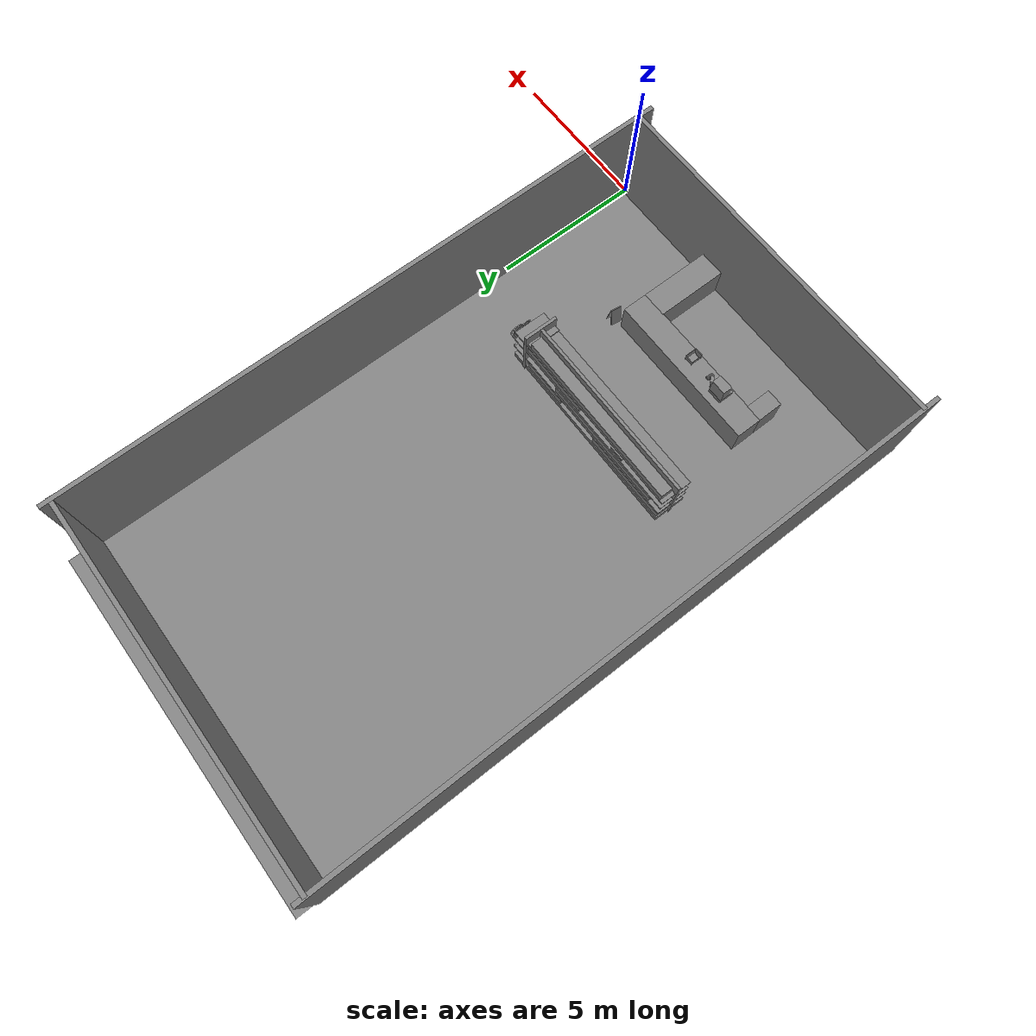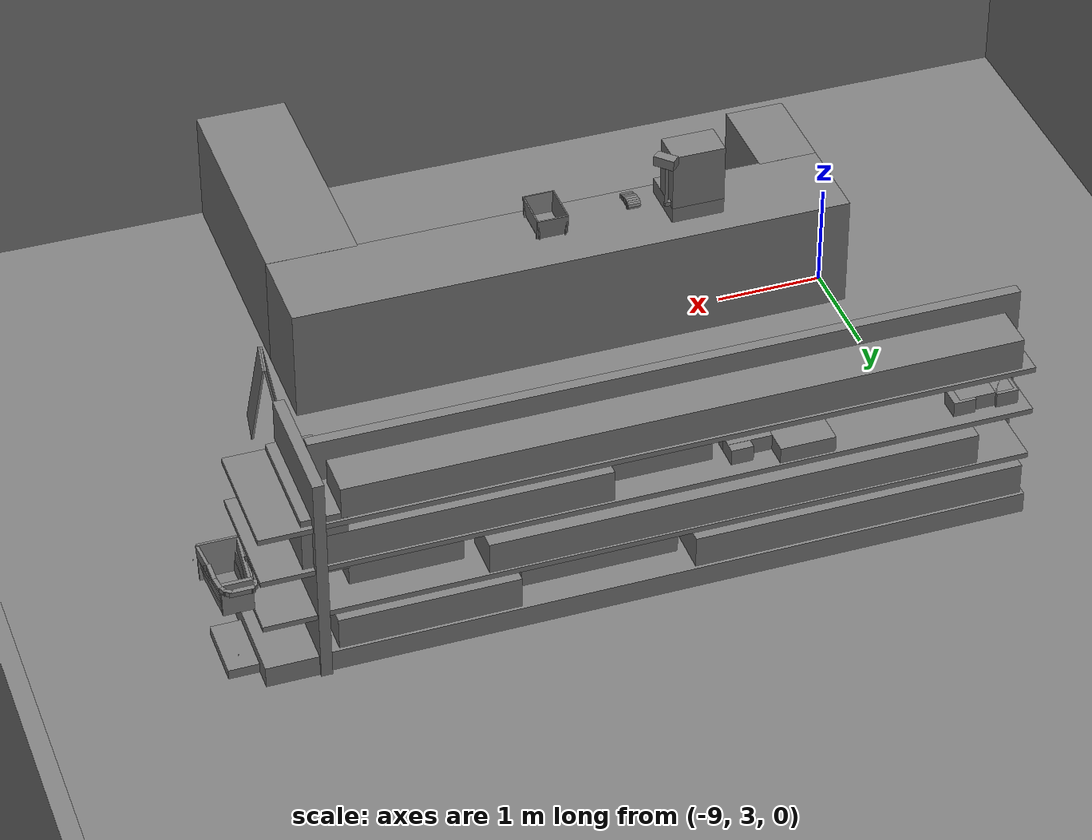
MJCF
<mujoco>
    <option gravity="0.000000000 0.000000000 -9.810000420" timestep="0.0166666" integrator="implicitfast" density="1.225" viscosity="1.8000001e-05" noslip_iterations="10" iterations="100" sdf_iterations="50">
        <flag multiccd="disable"/>
    </option>
    <size memory="1000M"/>
    <compiler coordinate="local"/>
    <worldbody>
        <light cutoff="30" pos="0 1 1" dir="0 -1 -2"/>
        <light cutoff="30" pos="0 -1 1" dir="0 1 -2"/>
        <body pos="-2.436573029 6.404376507 0.137849092" euler="0.000000000 0.000000000 0.000000000" name="openloong_gripper_2f85_fix_base_usda_shoppingtrolley_01">
            <geom contype="1" conaffinity="1" density="1000" type="box" material="" rgba="0.500000000 0.500000000 0.500000000 1.000000000" solimp="0.899999976 0.949999988 0.001000000" friction="1.000000000 0.005000000 0.000100000" solref="0.020000000 1.000000000" margin="0" condim="3" group="0" pos="-0.107458733 0.238907143 0.911498845" quat="0.634576976 0.622505128 -0.330067992 -0.317575932" size="0.017999999 0.022499999 0.035999998" name="openloong_gripper_2f85_fix_base_usda_geom_DBE5A126_76A9_421F_8A7F_F5C2066AA081"/>
            <geom contype="1" conaffinity="1" density="1000" type="box" material="" rgba="0.500000000 0.500000000 0.500000000 1.000000000" solimp="0.899999976 0.949999988 0.001000000" friction="1.000000000 0.005000000 0.000100000" solref="0.020000000 1.000000000" margin="0" condim="3" group="0" pos="-0.126757339 -0.182533979 0.598989725" quat="0.996607184 0.055331606 -0.059003651 -0.015205891" size="0.013499999 0.287999988 0.053999998" name="openloong_gripper_2f85_fix_base_usda_geom_916C3D4C_4493_4A12_B4E1_AD892D51BE47"/>
            <geom contype="1" conaffinity="1" density="1000" type="box" material="" rgba="0.500000000 0.500000000 0.500000000 1.000000000" solimp="0.899999976 0.949999988 0.001000000" friction="1.000000000 0.005000000 0.000100000" solref="0.020000000 1.000000000" margin="0" condim="3" group="0" pos="-0.005004787 0.248085022 0.912686050" quat="1.000000000 0.000000000 0.000000000 0.000000000" size="0.107999995 0.022499999 0.022499999" name="openloong_gripper_2f85_fix_base_usda_geom_C904C93F_5CD1_4325_91EF_7C55314F35B2"/>
            <geom contype="1" conaffinity="1" density="1000" type="box" material="" rgba="0.500000000 0.500000000 0.500000000 1.000000000" solimp="0.899999976 0.949999988 0.001000000" friction="1.000000000 0.005000000 0.000100000" solref="0.020000000 1.000000000" margin="0" condim="3" group="0" pos="-0.169898406 -0.043119621 0.915120542" quat="0.687021017 0.726584017 -0.005590606 -0.006832919" size="0.017999999 0.022499999 0.089999996" name="openloong_gripper_2f85_fix_base_usda_geom_41BE4C14_0F25_4C50_BFCD_2CCABED1FE81"/>
            <geom contype="1" conaffinity="1" density="1000" type="box" material="" rgba="0.500000000 0.500000000 0.500000000 1.000000000" solimp="0.899999976 0.949999988 0.001000000" friction="1.000000000 0.005000000 0.000100000" solref="0.020000000 1.000000000" margin="0" condim="3" group="0" pos="0.148195267 -0.199506566 0.782808602" quat="0.998808920 0.017156634 0.026950166 0.036880098" size="0.013499999 0.305999994 0.063000001" name="openloong_gripper_2f85_fix_base_usda_geom_33496DC4_C6FF_427A_B246_FA45739390A0"/>
            <geom contype="1" conaffinity="1" density="1000" type="box" material="" rgba="0.500000000 0.500000000 0.500000000 1.000000000" solimp="0.899999976 0.949999988 0.001000000" friction="1.000000000 0.005000000 0.000100000" solref="0.020000000 1.000000000" margin="0" condim="3" group="0" pos="-0.142927840 -0.199506134 0.784674108" quat="0.998421252 0.016904408 -0.027109101 -0.046199299" size="0.013499999 0.305999994 0.063000001" name="openloong_gripper_2f85_fix_base_usda_geom_D37CDEF6_1F01_49A0_B472_91BF71F34D27"/>
            <geom contype="1" conaffinity="1" density="1000" type="box" material="" rgba="0.500000000 0.500000000 0.500000000 1.000000000" solimp="0.899999976 0.949999988 0.001000000" friction="1.000000000 0.005000000 0.000100000" solref="0.020000000 1.000000000" margin="0" condim="3" group="0" pos="-0.000004721 -0.174527690 0.560063601" quat="0.996704638 0.081116498 -0.000000004 0.000000000" size="0.126000002 0.287999988 0.009000000" name="openloong_gripper_2f85_fix_base_usda_geom_622446F0_2A22_4D13_9D02_C5342A9F2C73"/>
            <geom contype="1" conaffinity="1" density="1000" type="box" material="" rgba="0.500000000 0.500000000 0.500000000 1.000000000" solimp="0.899999976 0.949999988 0.001000000" friction="1.000000000 0.005000000 0.000100000" solref="0.020000000 1.000000000" margin="0" condim="3" group="0" pos="-0.160832763 0.103427693 0.910528183" quat="0.711469591 0.699786782 -0.048386075 -0.042050660" size="0.017999999 0.022499999 0.071999997" name="openloong_gripper_2f85_fix_base_usda_geom_B42AC18A_CEE9_41CE_AD28_EE52775C20C7"/>
            <geom contype="1" conaffinity="1" density="1000" type="box" material="" rgba="0.500000000 0.500000000 0.500000000 1.000000000" solimp="0.899999976 0.949999988 0.001000000" friction="1.000000000 0.005000000 0.000100000" solref="0.020000000 1.000000000" margin="0" condim="3" group="0" pos="-0.169898406 -0.178061336 0.864131629" quat="0.916343808 -0.400392294 -0.000000045 0.000000030" size="0.017999999 0.022499999 0.089999996" name="openloong_gripper_2f85_fix_base_usda_geom_1A867904_18CB_4AA4_A926_5E37766EE50C"/>
            <geom contype="1" conaffinity="1" density="1000" type="box" material="" rgba="0.500000000 0.500000000 0.500000000 1.000000000" solimp="0.899999976 0.949999988 0.001000000" friction="1.000000000 0.005000000 0.000100000" solref="0.020000000 1.000000000" margin="0" condim="3" group="0" pos="-0.000006008 -0.484932661 0.670727849" quat="0.997585475 0.069449045 -0.000000004 -0.000000089" size="0.179999992 0.013499999 0.170999989" name="openloong_gripper_2f85_fix_base_usda_geom_0514EEB3_A485_400E_80D7_A896EE217F84"/>
            <geom contype="1" conaffinity="1" density="1000" type="box" material="" rgba="0.500000000 0.500000000 0.500000000 1.000000000" solimp="0.899999976 0.949999988 0.001000000" friction="1.000000000 0.005000000 0.000100000" solref="0.020000000 1.000000000" margin="0" condim="3" group="0" pos="0.134013891 0.200098798 0.912192523" quat="0.692574680 -0.680924535 -0.166899428 0.169783980" size="0.017999999 0.022499999 0.035999998" name="openloong_gripper_2f85_fix_base_usda_geom_424287E9_DE2E_4409_8B11_88DD70C92ED5"/>
            <geom contype="1" conaffinity="1" density="1000" type="box" material="" rgba="0.500000000 0.500000000 0.500000000 1.000000000" solimp="0.899999976 0.949999988 0.001000000" friction="1.000000000 0.005000000 0.000100000" solref="0.020000000 1.000000000" margin="0" condim="3" group="0" pos="0.141839072 -0.191051379 0.702451229" quat="0.997147262 0.056065105 0.045779929 0.021407485" size="0.013499999 0.287999988 0.053999998" name="openloong_gripper_2f85_fix_base_usda_geom_2767143C_2971_4044_8208_512A15E24A5E"/>
            <geom contype="1" conaffinity="1" density="1000" type="box" material="" rgba="0.500000000 0.500000000 0.500000000 1.000000000" solimp="0.899999976 0.949999988 0.001000000" friction="1.000000000 0.005000000 0.000100000" solref="0.020000000 1.000000000" margin="0" condim="3" group="0" pos="0.169898629 -0.178061336 0.864131629" quat="0.916343808 -0.400392294 -0.000000045 0.000000030" size="0.017999999 0.022499999 0.089999996" name="openloong_gripper_2f85_fix_base_usda_geom_EBB0E335_1129_4500_B1D6_56C62E47E9A0"/>
            <geom contype="1" conaffinity="1" density="1000" type="box" material="" rgba="0.500000000 0.500000000 0.500000000 1.000000000" solimp="0.899999976 0.949999988 0.001000000" friction="1.000000000 0.005000000 0.000100000" solref="0.020000000 1.000000000" margin="0" condim="3" group="0" pos="-0.000005364 0.100332208 0.734785020" quat="0.999668717 0.025737956 -0.000000010 0.000000000" size="0.135000005 0.019800000 0.152999997" name="openloong_gripper_2f85_fix_base_usda_geom_9BB722DB_303D_4740_AC92_BCA882609216"/>
            <geom contype="1" conaffinity="1" density="1000" type="box" material="" rgba="0.500000000 0.500000000 0.500000000 1.000000000" solimp="0.899999976 0.949999988 0.001000000" friction="1.000000000 0.005000000 0.000100000" solref="0.020000000 1.000000000" margin="0" condim="3" group="0" pos="-0.012634277 -0.174527690 -0.088243507" quat="1.000000000 0.000000000 -0.000000004 0.000000000" size="0.135000005 0.287999988 0.044999998" name="openloong_gripper_2f85_fix_base_usda_geom_AF9E6ABF_6F99_4F10_BAB0_947C2DABAE4B"/>
            <geom contype="1" conaffinity="1" density="1000" type="box" material="" rgba="0.500000000 0.500000000 0.500000000 1.000000000" solimp="0.899999976 0.949999988 0.001000000" friction="1.000000000 0.005000000 0.000100000" solref="0.020000000 1.000000000" margin="0" condim="3" group="0" pos="0.131482959 -0.182533979 0.598989725" quat="0.996607125 0.055331629 0.059003670 0.015205893" size="0.013499999 0.287999988 0.053999998" name="openloong_gripper_2f85_fix_base_usda_geom_39E61776_CCDF_469E_8C93_3F852B539FAA"/>
            <geom contype="1" conaffinity="1" density="1000" type="box" material="" rgba="0.500000000 0.500000000 0.500000000 1.000000000" solimp="0.899999976 0.949999988 0.001000000" friction="1.000000000 0.005000000 0.000100000" solref="0.020000000 1.000000000" margin="0" condim="3" group="0" pos="0.103667587 0.233050480 0.912927270" quat="0.634205043 -0.622199059 -0.324503720 0.324576139" size="0.017999999 0.022499999 0.035999998" name="openloong_gripper_2f85_fix_base_usda_geom_886455F5_3400_4459_AE7E_3E3A9E9B68F2"/>
            <geom contype="1" conaffinity="1" density="1000" type="box" material="" rgba="0.500000000 0.500000000 0.500000000 1.000000000" solimp="0.899999976 0.949999988 0.001000000" friction="1.000000000 0.005000000 0.000100000" solref="0.020000000 1.000000000" margin="0" condim="3" group="0" pos="-0.134013891 0.200098798 0.912192523" quat="0.694057047 0.679413557 -0.172947660 -0.163618833" size="0.017999999 0.022499999 0.035999998" name="openloong_gripper_2f85_fix_base_usda_geom_8BD2CD0B_B54F_4068_8E3E_FC7432C8E2BE"/>
            <geom contype="1" conaffinity="1" density="1000" type="box" material="" rgba="0.500000000 0.500000000 0.500000000 1.000000000" solimp="0.899999976 0.949999988 0.001000000" friction="1.000000000 0.005000000 0.000100000" solref="0.020000000 1.000000000" margin="0" condim="3" group="0" pos="-0.135714188 -0.191051379 0.694841146" quat="0.997147322 0.056064609 -0.045779683 -0.021407485" size="0.013499999 0.287999988 0.053999998" name="openloong_gripper_2f85_fix_base_usda_geom_D5461190_E2AE_4FCB_9250_0FC84455276C"/>
            <geom contype="1" conaffinity="1" density="1000" type="box" material="" rgba="0.500000000 0.500000000 0.500000000 1.000000000" solimp="0.899999976 0.949999988 0.001000000" friction="1.000000000 0.005000000 0.000100000" solref="0.020000000 1.000000000" margin="0" condim="3" group="0" pos="0.169898629 -0.043119621 0.915120542" quat="0.687029123 -0.726576388 -0.006509603 0.005963952" size="0.017999999 0.022499999 0.089999996" name="openloong_gripper_2f85_fix_base_usda_geom_1D4FB2DE_7939_47A3_A31E_E2835232F3E6"/>
            <geom contype="1" conaffinity="1" density="1000" type="box" material="" rgba="0.500000000 0.500000000 0.500000000 1.000000000" solimp="0.899999976 0.949999988 0.001000000" friction="1.000000000 0.005000000 0.000100000" solref="0.020000000 1.000000000" margin="0" condim="3" group="0" pos="0.160832971 0.103427693 0.910528183" quat="0.711112797 -0.700149298 -0.042821646 0.047705106" size="0.017999999 0.022499999 0.071999997" name="openloong_gripper_2f85_fix_base_usda_geom_C70EA5D9_EB85_4EC1_973B_C10F13D333A5"/>
            <freejoint name="openloong_gripper_2f85_fix_base_usda_shoppingtrolley_01_joint"/>
            <site size="0.005000000 0.005000000 0.005000000" rgba="0.500000000 0.500000000 0.500000000 1.000000000" pos="0.000000000 0.000000000 0.000000000" quat="1.000000000 0.000000000 0.000000000 0.000000000" group="0" type="sphere" name="openloong_gripper_2f85_fix_base_usda_shoppingtrolley_01"/>
        </body>
        <body pos="-7.168000221 2.823999882 1.227496982" euler="-0.283413887 0.056829713 -0.133293241" name="openloong_gripper_2f85_fix_base_usda_Pos">
            <geom contype="1" conaffinity="1" density="1000" type="box" material="" rgba="0.500000000 0.500000000 0.500000000 1.000000000" solimp="0.899999976 0.949999988 0.001000000" friction="1.000000000 0.005000000 0.000100000" solref="0.020000000 1.000000000" margin="0" condim="3" group="0" pos="-0.002278805 0.074524641 -0.004134178" quat="0.315989256 0.948762834 0.000000000 0.000000000" size="0.059999999 0.013000000 0.035000000" name="openloong_gripper_2f85_fix_base_usda_geom_3CDE3D5B_DB0D_4068_8CB0_0043C7D9ECF0"/>
            <geom contype="1" conaffinity="1" density="1000" type="box" material="" rgba="0.500000000 0.500000000 0.500000000 1.000000000" solimp="0.899999976 0.949999988 0.001000000" friction="1.000000000 0.005000000 0.000100000" solref="0.020000000 1.000000000" margin="0" condim="3" group="0" pos="-0.002278805 0.078031301 0.008128285" quat="0.990447283 -0.137893349 -0.000000000 0.000000000" size="0.059999999 0.010000000 0.035000000" name="openloong_gripper_2f85_fix_base_usda_geom_DAB0C112_45A1_47C0_8D7A_589F155BE3CB"/>
            <geom contype="1" conaffinity="1" density="1000" type="box" material="" rgba="0.500000000 0.500000000 0.500000000 1.000000000" solimp="0.899999976 0.949999988 0.001000000" friction="1.000000000 0.005000000 0.000100000" solref="0.020000000 1.000000000" margin="0" condim="3" group="0" pos="-0.002278805 0.080785275 -0.002596974" quat="0.287325412 -0.957833171 0.000000000 -0.000000000" size="0.059999999 0.013000000 0.035000000" name="openloong_gripper_2f85_fix_base_usda_geom_758CE3A0_3C31_43F2_80B1_B075CD5BE17F"/>
            <geom contype="1" conaffinity="1" density="1000" type="box" material="" rgba="0.500000000 0.500000000 0.500000000 1.000000000" solimp="0.899999976 0.949999988 0.001000000" friction="1.000000000 0.005000000 0.000100000" solref="0.020000000 1.000000000" margin="0" condim="3" group="0" pos="-0.002278805 -0.098804474 -0.020147085" quat="0.988851428 0.148906425 0.000000000 -0.000000000" size="0.059999999 0.022000000 0.020000000" name="openloong_gripper_2f85_fix_base_usda_geom_6BB57C50_6B01_4408_A05A_0E65D1DDBDB6"/>
            <geom contype="1" conaffinity="1" density="1000" type="box" material="" rgba="0.500000000 0.500000000 0.500000000 1.000000000" solimp="0.899999976 0.949999988 0.001000000" friction="1.000000000 0.005000000 0.000100000" solref="0.020000000 1.000000000" margin="0" condim="3" group="0" pos="-0.002279282 0.019920349 0.012102842" quat="0.995421529 0.095583312 -0.000000000 0.000000000" size="0.059999999 0.025000000 0.026000001" name="openloong_gripper_2f85_fix_base_usda_geom_E080A74C_C6B2_470D_81C6_9B829AF4058B"/>
            <geom contype="1" conaffinity="1" density="1000" type="box" material="" rgba="0.500000000 0.500000000 0.500000000 1.000000000" solimp="0.899999976 0.949999988 0.001000000" friction="1.000000000 0.005000000 0.000100000" solref="0.020000000 1.000000000" margin="0" condim="3" group="0" pos="-0.002279282 0.005734444 -0.014276981" quat="0.999571502 -0.029275293 -0.000000000 0.000000000" size="0.059999999 0.050000001 0.010000000" name="openloong_gripper_2f85_fix_base_usda_geom_FC0DFB65_2D59_4708_AB84_D0868E273D92"/>
            <geom contype="1" conaffinity="1" density="1000" type="box" material="" rgba="0.500000000 0.500000000 0.500000000 1.000000000" solimp="0.899999976 0.949999988 0.001000000" friction="1.000000000 0.005000000 0.000100000" solref="0.020000000 1.000000000" margin="0" condim="3" group="0" pos="-0.002278805 0.079460382 0.007771969" quat="0.922590315 -0.385781497 -0.000000000 0.000000000" size="0.059999999 0.010000000 0.035000000" name="openloong_gripper_2f85_fix_base_usda_geom_E534E6B9_5136_4675_B640_560F037C816C"/>
            <geom contype="1" conaffinity="1" density="1000" type="box" material="" rgba="0.500000000 0.500000000 0.500000000 1.000000000" solimp="0.899999976 0.949999988 0.001000000" friction="1.000000000 0.005000000 0.000100000" solref="0.020000000 1.000000000" margin="0" condim="3" group="0" pos="-0.002279282 0.081384182 -0.001320124" quat="0.590483606 -0.807049692 0.000000000 0.000000000" size="0.059999999 0.013000000 0.035000000" name="openloong_gripper_2f85_fix_base_usda_geom_2AAC0377_1697_4A44_8D08_1E7F9A22A47E"/>
            <geom contype="1" conaffinity="1" density="1000" type="box" material="" rgba="0.500000000 0.500000000 0.500000000 1.000000000" solimp="0.899999976 0.949999988 0.001000000" friction="1.000000000 0.005000000 0.000100000" solref="0.020000000 1.000000000" margin="0" condim="3" group="0" pos="-0.002278805 -0.059297562 -0.007972836" quat="0.988851428 0.148906425 0.000000000 -0.000000000" size="0.059999999 0.020000000 0.022000000" name="openloong_gripper_2f85_fix_base_usda_geom_EA97D440_684C_42F7_AFC2_2F7847C7DD54"/>
            <geom contype="1" conaffinity="1" density="1000" type="box" material="" rgba="0.500000000 0.500000000 0.500000000 1.000000000" solimp="0.899999976 0.949999988 0.001000000" friction="1.000000000 0.005000000 0.000100000" solref="0.020000000 1.000000000" margin="0" condim="3" group="0" pos="-0.002278805 0.076618671 -0.004656911" quat="0.004634960 0.999989390 -0.000000000 0.000000000" size="0.059999999 0.013000000 0.035000000" name="openloong_gripper_2f85_fix_base_usda_geom_9FC8BB43_524B_46ED_8512_163B64B723AD"/>
            <geom contype="1" conaffinity="1" density="1000" type="box" material="" rgba="0.500000000 0.500000000 0.500000000 1.000000000" solimp="0.899999976 0.949999988 0.001000000" friction="1.000000000 0.005000000 0.000100000" solref="0.020000000 1.000000000" margin="0" condim="3" group="0" pos="-0.002279282 -0.021952629 0.002959967" quat="0.991270185 0.131847635 0.000000000 -0.000000000" size="0.059999999 0.020000000 0.024000000" name="openloong_gripper_2f85_fix_base_usda_geom_0DD5CEB7_3225_4DE2_9E63_300DFE1F698C"/>
            <geom contype="1" conaffinity="1" density="1000" type="box" material="" rgba="0.500000000 0.500000000 0.500000000 1.000000000" solimp="0.899999976 0.949999988 0.001000000" friction="1.000000000 0.005000000 0.000100000" solref="0.020000000 1.000000000" margin="0" condim="3" group="0" pos="-0.002278805 0.081418991 0.002587795" quat="0.803492188 -0.595315576 0.000000000 0.000000000" size="0.059999999 0.013000000 0.035000000" name="openloong_gripper_2f85_fix_base_usda_geom_317DB5C4_87BD_4526_B461_B5AD673863E2"/>
            <geom contype="1" conaffinity="1" density="1000" type="box" material="" rgba="0.500000000 0.500000000 0.500000000 1.000000000" solimp="0.899999976 0.949999988 0.001000000" friction="1.000000000 0.005000000 0.000100000" solref="0.020000000 1.000000000" margin="0" condim="3" group="0" pos="-0.002278805 0.061115503 0.008545756" quat="0.999325931 0.036714435 -0.000000000 -0.000000000" size="0.059999999 0.020000000 0.035000000" name="openloong_gripper_2f85_fix_base_usda_geom_48804DCA_7050_46BA_B455_A11B4067104C"/>
            <freejoint name="openloong_gripper_2f85_fix_base_usda_pos_scan"/>
        </body>
        <body pos="-3.510578632 3.403555870 -0.000000100" euler="0.000000000 0.000000000 40.200675964" name="openloong_gripper_2f85_fix_base_usda_PZ">
            <geom contype="1" conaffinity="1" density="1000" type="box" material="" rgba="0.500000000 0.500000000 0.500000000 1.000000000" solimp="0.899999976 0.949999988 0.001000000" friction="1.000000000 0.005000000 0.000100000" solref="0.020000000 1.000000000" margin="0" condim="3" group="0" pos="-0.047453165 0.056484699 0.373715430" quat="0.934750080 0.077914521 0.028795123 0.345459938" size="0.180000007 0.010000000 0.379999995" name="openloong_gripper_2f85_fix_base_usda_geom_1A9D31D0_D942_4E28_8B38_DA8FD69CCF05"/>
            <geom contype="1" conaffinity="1" density="1000" type="box" material="" rgba="0.500000000 0.500000000 0.500000000 1.000000000" solimp="0.899999976 0.949999988 0.001000000" friction="1.000000000 0.005000000 0.000100000" solref="0.020000000 1.000000000" margin="0" condim="3" group="0" pos="0.047452450 -0.054376602 0.374072611" quat="0.934387863 -0.082143910 -0.030358355 0.345326364" size="0.180000007 0.010000000 0.379999995" name="openloong_gripper_2f85_fix_base_usda_geom_4849D9F0_20C2_4123_B959_AE10C7190032"/>
            <freejoint name="openloong_gripper_2f85_fix_base_usda_PZ"/>
        </body>
        <body pos="-6.332345009 2.779978037 1.034067392" euler="0.000000000 0.000000000 0.000000000" name="openloong_gripper_2f85_fix_base_usda_basket">
            <geom contype="1" conaffinity="1" density="100000" type="box" material="" rgba="0.500000000 0.500000000 0.500000000 1.000000000" solimp="0.899999976 0.949999988 0.001000000" friction="1.000000000 0.899999976 0.000100000" solref="0.020000000 1.000000000" margin="0" condim="3" group="0" pos="-0.039724827 -0.188568115 0.167089701" quat="0.997537494 0.070135131 0.000000000 0.000000000" size="0.150000006 0.006000000 0.108000003" name="openloong_gripper_2f85_fix_base_usda_geom_9CC5634E_913A_4DD9_A0C1_73D4754FD0EA"/>
            <geom contype="1" conaffinity="1" density="100000" type="box" material="" rgba="0.500000000 0.500000000 0.500000000 1.000000000" solimp="0.899999976 0.949999988 0.001000000" friction="1.000000000 0.899999976 0.000100000" solref="0.020000000 1.000000000" margin="0" condim="3" group="0" pos="0.094372749 0.000000000 0.168361664" quat="0.706172049 0.036353335 0.036353379 0.706171215" size="0.200000003 0.006000000 0.108000003" name="openloong_gripper_2f85_fix_base_usda_geom_AF31152E_01B8_4108_89A9_D3735916EB61"/>
            <geom contype="1" conaffinity="1" density="100000" type="box" material="" rgba="0.500000000 0.500000000 0.500000000 1.000000000" solimp="0.899999976 0.949999988 0.001000000" friction="1.000000000 0.899999976 0.000100000" solref="0.020000000 1.000000000" margin="0" condim="3" group="0" pos="-0.039724827 0.000000000 0.068126202" quat="1.000000000 0.000000000 0.000000000 0.000000000" size="0.129999995 0.174999997 0.006000000" name="openloong_gripper_2f85_fix_base_usda_geom_7341F1D6_31F5_4D24_9BAB_65DCCF55F57D"/>
            <geom contype="1" conaffinity="1" density="100000" type="box" material="" rgba="0.500000000 0.500000000 0.500000000 1.000000000" solimp="0.899999976 0.949999988 0.001000000" friction="1.000000000 0.899999976 0.000100000" solref="0.020000000 1.000000000" margin="0" condim="3" group="0" pos="-0.039724827 0.188377380 0.167089701" quat="0.997489929 -0.070808925 0.000000000 0.000000000" size="0.150000006 0.006000000 0.108000003" name="openloong_gripper_2f85_fix_base_usda_geom_FD02D5EF_BBE5_4E05_8AE2_021CCF78809A"/>
            <geom contype="1" conaffinity="1" density="100000" type="box" material="" rgba="0.500000000 0.500000000 0.500000000 1.000000000" solimp="0.899999976 0.949999988 0.001000000" friction="1.000000000 0.899999976 0.000100000" solref="0.020000000 1.000000000" margin="0" condim="3" group="0" pos="-0.172339439 0.000000000 0.168361664" quat="0.706172407 -0.036353018 -0.036353093 0.706170976" size="0.200000003 0.006000000 0.108000003" name="openloong_gripper_2f85_fix_base_usda_geom_BB646488_F11B_4814_B2B0_9B6665B6501E"/>
            <freejoint name="openloong_gripper_2f85_fix_base_usda_basket_joint"/>
            <site size="0.005000000 0.005000000 0.005000000" rgba="0.500000000 0.500000000 0.500000000 1.000000000" pos="0.000000000 0.000000000 0.000000000" quat="1.000000000 0.000000000 0.000000000 0.000000000" group="0" type="sphere" name="openloong_gripper_2f85_fix_base_usda_basketsite"/>
        </body>
        <body pos="0.000000000 0.000000000 0.000000000" euler="0.000000000 0.000000000 0.000000000" name=" Static Objects_ Static Objects">
            <geom contype="1" conaffinity="1" density="1000" type="box" material="" rgba="0.500000000 0.500000000 0.500000000 1.000000000" solimp="0.899999976 0.949999988 0.001000000" friction="1.000000000 0.005000000 0.000100000" solref="0.020000000 1.000000000" margin="0" condim="3" group="0" pos="-6.286010742 6.153595448 1.563861728" quat="0.707107067 0.000000000 0.000000000 0.707106471" size="0.529999971 3.134999990 0.025000000" name=" Static Objects_geom_4D9DED15_9D1F_45C6_9F03_3E246F637213"/>
            <geom contype="1" conaffinity="1" density="1000" type="box" material="" rgba="0.500000000 0.500000000 0.500000000 1.000000000" solimp="0.899999976 0.949999988 0.001000000" friction="1.000000000 0.005000000 0.000100000" solref="0.020000000 1.000000000" margin="0" condim="3" group="0" pos="-3.101639986 6.150595188 1.018643856" quat="1.000000000 0.000000000 0.000000000 0.000000000" size="0.050000001 0.579999983 1.019999981" name=" Static Objects_geom_7FEF00AC_CCBA_4F03_8695_4A89B370A33D"/>
            <geom contype="1" conaffinity="1" density="1000" type="box" material="" rgba="0.500000000 0.500000000 0.500000000 1.000000000" solimp="0.899999976 0.949999988 0.001000000" friction="1.000000000 0.005000000 0.000100000" solref="0.020000000 1.000000000" margin="0" condim="3" group="0" pos="-2.825197220 6.153595448 1.563861728" quat="0.707107067 0.000000000 0.000000000 0.707106471" size="0.550000012 0.239999995 0.025000000" name=" Static Objects_geom_210AA4AB_FFDB_4D79_96A8_55C743937406"/>
            <geom contype="1" conaffinity="1" density="1000" type="box" material="" rgba="0.500000000 0.500000000 0.500000000 1.000000000" solimp="0.899999976 0.949999988 0.001000000" friction="1.000000000 0.005000000 0.000100000" solref="0.020000000 1.000000000" margin="0" condim="3" group="0" pos="-6.311686516 6.153595448 1.018643856" quat="0.707107067 0.000000000 0.000000000 0.707106471" size="0.050000001 3.150000095 1.019999981" name=" Static Objects_geom_5E2BA751_A9F7_417A_AD49_4D4E9EFF3AC7"/>
            <geom contype="1" conaffinity="1" density="1000" type="box" material="" rgba="0.500000000 0.500000000 0.500000000 1.000000000" solimp="0.899999976 0.949999988 0.001000000" friction="1.000000000 0.005000000 0.000100000" solref="0.020000000 1.000000000" margin="0" condim="3" group="0" pos="-2.825197220 6.153595448 1.115278244" quat="0.707107067 0.000000000 0.000000000 0.707106471" size="0.550000012 0.239999995 0.025000000" name=" Static Objects_geom_69B0129E_55E6_4146_A569_7FB900473B9B"/>
            <geom contype="1" conaffinity="1" density="1000" type="box" material="" rgba="0.500000000 0.500000000 0.500000000 1.000000000" solimp="0.899999976 0.949999988 0.001000000" friction="1.000000000 0.005000000 0.000100000" solref="0.020000000 1.000000000" margin="0" condim="3" group="0" pos="-6.293097973 6.153595448 1.114443064" quat="0.707107067 0.000000000 0.000000000 0.707106471" size="0.529999971 3.134999990 0.025000000" name=" Static Objects_geom_927D179F_4DDD_4D58_9F52_4316054274D7"/>
            <geom contype="1" conaffinity="1" density="1000" type="box" material="" rgba="0.500000000 0.500000000 0.500000000 1.000000000" solimp="0.899999976 0.949999988 0.001000000" friction="1.000000000 0.005000000 0.000100000" solref="0.020000000 1.000000000" margin="0" condim="3" group="0" pos="-2.825197220 6.153595448 0.629031777" quat="0.707107067 0.000000000 0.000000000 0.707106471" size="0.550000012 0.239999995 0.025000000" name=" Static Objects_geom_E9B590B6_5A2D_448A_8D89_24E4E532ADA6"/>
            <geom contype="1" conaffinity="1" density="1000" type="box" material="" rgba="0.500000000 0.500000000 0.500000000 1.000000000" solimp="0.899999976 0.949999988 0.001000000" friction="1.000000000 0.005000000 0.000100000" solref="0.020000000 1.000000000" margin="0" condim="3" group="0" pos="-6.286010742 6.153595448 0.096129179" quat="0.707107067 0.000000000 0.000000000 0.707106471" size="0.529999971 3.134999990 0.098999999" name=" Static Objects_geom_63EAFD4F_D3BD_43D8_9716_20661F0DEA64"/>
            <geom contype="1" conaffinity="1" density="1000" type="box" material="" rgba="0.500000000 0.500000000 0.500000000 1.000000000" solimp="0.899999976 0.949999988 0.001000000" friction="1.000000000 0.005000000 0.000100000" solref="0.020000000 1.000000000" margin="0" condim="3" group="0" pos="-2.825197220 6.153595448 0.097434282" quat="0.707107067 0.000000000 0.000000000 0.707106471" size="0.550000012 0.239999995 0.098999999" name=" Static Objects_geom_98A4089C_15D9_4A0B_B62B_1A768CA872B4"/>
            <geom contype="1" conaffinity="1" density="1000" type="box" material="" rgba="0.500000000 0.500000000 0.500000000 1.000000000" solimp="0.899999976 0.949999988 0.001000000" friction="1.000000000 0.005000000 0.000100000" solref="0.020000000 1.000000000" margin="0" condim="3" group="0" pos="-6.286010742 6.153595448 0.629031777" quat="0.707107067 0.000000000 0.000000000 0.707106471" size="0.529999971 3.134999990 0.025000000" name=" Static Objects_geom_AC2C6B62_9C9F_4762_9A5D_CAFBF4F07E9F"/>
            <geom contype="1" conaffinity="1" density="1000" type="box" material="" rgba="0.500000000 0.500000000 0.500000000 1.000000000" solimp="0.899999976 0.949999988 0.001000000" friction="1.000000000 0.005000000 0.000100000" solref="0.020000000 1.000000000" margin="0" condim="3" group="0" pos="-6.000000000 20.159999847 2.000000000" quat="1.000000000 0.000000000 0.000000000 0.000000000" size="6.079999924 0.070000000 2.000000000" name=" Static Objects_geom_B0FB0338_7C29_4A38_917B_CE05D9656FA0"/>
            <geom contype="1" conaffinity="1" density="1000" type="box" material="" rgba="0.500000000 0.500000000 0.500000000 1.000000000" solimp="0.899999976 0.949999988 0.001000000" friction="1.000000000 0.005000000 0.000100000" solref="0.020000000 1.000000000" margin="0" condim="3" group="0" pos="-6.000000000 0.035000000 2.000000000" quat="1.000000000 0.000000000 0.000000000 0.000000000" size="6.079999924 0.070000000 2.000000000" name=" Static Objects_geom_FC96A8E3_3E89_489B_A4F5_9B6A0E1D7B35"/>
            <geom contype="1" conaffinity="1" density="1000" type="box" material="" rgba="0.500000000 0.500000000 0.500000000 1.000000000" solimp="0.899999976 0.949999988 0.001000000" friction="1.000000000 0.005000000 0.000100000" solref="0.020000000 1.000000000" margin="0" condim="3" group="0" pos="0.000000000 10.000000000 2.000000000" quat="1.000000000 0.000000000 0.000000000 0.000000000" size="0.070000000 10.500000000 2.000000000" name=" Static Objects_geom_307867FB_E5C2_48F2_904D_54E6A8F6F945"/>
            <geom contype="1" conaffinity="1" density="1000" type="box" material="" rgba="0.500000000 0.500000000 0.500000000 1.000000000" solimp="0.899999976 0.949999988 0.001000000" friction="1.000000000 0.005000000 0.000100000" solref="0.020000000 1.000000000" margin="0" condim="3" group="0" pos="-12.050000191 10.000000000 2.000000000" quat="1.000000000 0.000000000 0.000000000 0.000000000" size="0.070000000 10.500000000 2.000000000" name=" Static Objects_geom_F85EB228_8952_42E7_B03F_AFF1A0E22D68"/>
            <geom contype="1" conaffinity="1" density="1000" type="plane" material="" rgba="0.500000000 0.500000000 0.500000000 1.000000000" solimp="0.899999976 0.949999988 0.001000000" friction="1.000000000 0.005000000 0.000100000" solref="0.020000000 1.000000000" margin="0" condim="3" group="0" pos="-6.000000000 10.399999619 0.000000000" quat="1.000000000 0.000000000 0.000000000 0.000000000" size="6.050000191 10.800000191 0.010000000" name=" Static Objects_geom_ECBFDBF2_F645_4D1E_AA5C_1514233C1D52"/>
            <geom contype="1" conaffinity="1" density="1000" type="box" material="" rgba="0.500000000 0.500000000 0.500000000 1.000000000" solimp="0.899999976 0.949999988 0.001000000" friction="1.000000000 0.005000000 0.000100000" solref="0.020000000 1.000000000" margin="0" condim="3" group="0" pos="-8.830721855 2.096410990 0.549305558" quat="1.000000000 0.000000000 0.000000000 0.000000000" size="0.280000001 0.430000007 0.550000012" name=" Static Objects_geom_EE23B4F5_B6A7_4CAA_BC58_FD6BAB69F0B4"/>
            <geom contype="1" conaffinity="1" density="1000" type="box" material="" rgba="0.500000000 0.500000000 0.500000000 1.000000000" solimp="0.899999976 0.949999988 0.001000000" friction="1.000000000 0.005000000 0.000100000" solref="0.020000000 1.000000000" margin="0" condim="3" group="0" pos="-6.460197449 2.937205315 0.548931718" quat="1.000000000 0.000000000 0.000000000 0.000000000" size="2.650000095 0.430000007 0.550000012" name=" Static Objects_geom_2DE1A272_74BA_4494_9588_8A520C6B18BA"/>
            <geom contype="1" conaffinity="1" density="1000" type="box" material="" rgba="0.500000000 0.500000000 0.500000000 1.000000000" solimp="0.899999976 0.949999988 0.001000000" friction="1.000000000 0.005000000 0.000100000" solref="0.020000000 1.000000000" margin="0" condim="3" group="0" pos="-4.240264893 1.327049494 0.549888909" quat="1.000000000 0.000000000 0.000000000 0.000000000" size="0.430000007 1.200000048 0.550000012" name=" Static Objects_geom_A42AEE42_7D10_4FA2_8450_D19B1AD73E83"/>
            <geom contype="1" conaffinity="1" density="1000" type="box" material="" rgba="0.500000000 0.500000000 0.500000000 1.000000000" solimp="0.899999976 0.949999988 0.001000000" friction="1.000000000 0.005000000 0.000100000" solref="0.020000000 1.000000000" margin="0" condim="3" group="0" pos="-7.408766270 3.088089943 1.776644945" quat="0.928051054 0.000000000 0.000000000 0.372453064" size="0.050000001 0.100000001 0.050000001" name=" Static Objects_geom_64319DB4_45E5_4261_9A08_1B9802198F4D"/>
            <geom contype="1" conaffinity="1" density="1000" type="box" material="" rgba="0.500000000 0.500000000 0.500000000 1.000000000" solimp="0.899999976 0.949999988 0.001000000" friction="1.000000000 0.005000000 0.000100000" solref="0.020000000 1.000000000" margin="0" condim="3" group="0" pos="-7.437745571 3.067511320 1.289965630" quat="1.000000000 0.000000000 0.000000000 0.000000000" size="0.029999999 0.020000000 0.020000000" name=" Static Objects_geom_EF22FD43_C77A_4D0E_B596_0A822F0234A7"/>
            <geom contype="1" conaffinity="1" density="1000" type="box" material="" rgba="0.500000000 0.500000000 0.500000000 1.000000000" solimp="0.899999976 0.949999988 0.001000000" friction="1.000000000 0.005000000 0.000100000" solref="0.020000000 1.000000000" margin="0" condim="3" group="0" pos="-7.719123363 2.867671013 1.173410416" quat="1.000000000 0.000000000 0.000000000 0.000000000" size="0.250000000 0.250000000 0.079999998" name=" Static Objects_geom_06D17F2B_D6AF_4015_B16D_77F14797C501"/>
            <geom contype="1" conaffinity="1" density="1000" type="box" material="" rgba="0.500000000 0.500000000 0.500000000 1.000000000" solimp="0.899999976 0.949999988 0.001000000" friction="1.000000000 0.005000000 0.000100000" solref="0.020000000 1.000000000" margin="0" condim="3" group="0" pos="-7.719123363 2.958004713 1.530241251" quat="1.000000000 0.000000000 0.000000000 0.000000000" size="0.250000000 0.159999996 0.280000001" name=" Static Objects_geom_913A838C_7D49_4E9F_8E4B_6088B9C5D8EA"/>
            <geom contype="1" conaffinity="1" density="1000" type="cylinder" material="" rgba="0.500000000 0.500000000 0.500000000 1.000000000" solimp="0.899999976 0.949999988 0.001000000" friction="1.000000000 0.005000000 0.000100000" solref="0.020000000 1.000000000" margin="0" condim="3" group="0" pos="-7.427312374 3.069516420 1.502544641" quat="0.928051054 0.000000000 0.000000000 0.372453064" size="0.015000000 0.230000004 0.100000001" name=" Static Objects_geom_4E387DAC_BA62_4EFD_9FD5_5ACAFA2AB10A"/>
            <geom contype="1" conaffinity="1" density="1000" type="box" material="" rgba="0.500000000 0.500000000 0.500000000 1.000000000" solimp="0.899999976 0.949999988 0.001000000" friction="1.000000000 0.005000000 0.000100000" solref="0.020000000 1.000000000" margin="0" condim="3" group="0" pos="-9.058088303 6.434794426 1.209077358" quat="1.000000000 0.000000000 0.000000000 0.000000000" size="0.250000000 0.100000001 0.070000000" name=" Static Objects_geom_07DCBEA8_E329_4C5E_AEAF_0A36D0AC008F"/>
            <geom contype="1" conaffinity="1" density="1000" type="box" material="" rgba="0.500000000 0.500000000 0.500000000 1.000000000" solimp="0.899999976 0.949999988 0.001000000" friction="1.000000000 0.005000000 0.000100000" solref="0.020000000 1.000000000" margin="0" condim="3" group="0" pos="-5.611940861 6.318420410 0.350975692" quat="1.000000000 0.000000000 0.000000000 0.000000000" size="0.699999988 0.100000001 0.150000006" name=" Static Objects_geom_FB5C8842_3936_46D5_A428_00CB3FDA91FB"/>
            <geom contype="1" conaffinity="1" density="1000" type="box" material="" rgba="0.500000000 0.500000000 0.500000000 1.000000000" solimp="0.899999976 0.949999988 0.001000000" friction="1.000000000 0.005000000 0.000100000" solref="0.020000000 1.000000000" margin="0" condim="3" group="0" pos="-9.237723351 6.464855671 1.209077358" quat="1.000000000 0.000000000 0.000000000 0.000000000" size="0.100000001 0.100000001 0.070000000" name=" Static Objects_geom_FF1BAC90_B53A_4A8C_95F2_0CD5D1180B1D"/>
            <geom contype="1" conaffinity="1" density="1000" type="box" material="" rgba="0.500000000 0.500000000 0.500000000 1.000000000" solimp="0.899999976 0.949999988 0.001000000" friction="1.000000000 0.005000000 0.000100000" solref="0.020000000 1.000000000" margin="0" condim="3" group="0" pos="-6.300771236 6.459744930 1.744376063" quat="1.000000000 0.000000000 0.000000000 0.000000000" size="3.000000000 0.200000003 0.150000006" name=" Static Objects_geom_2AF8320A_F1A8_4932_825E_5F0CB1E05CAF"/>
            <geom contype="1" conaffinity="1" density="1000" type="box" material="" rgba="0.500000000 0.500000000 0.500000000 1.000000000" solimp="0.899999976 0.949999988 0.001000000" friction="1.000000000 0.005000000 0.000100000" solref="0.020000000 1.000000000" margin="0" condim="3" group="0" pos="-7.373087406 6.458900928 1.214329123" quat="1.000000000 0.000000000 0.000000000 0.000000000" size="0.250000000 0.200000003 0.075000003" name=" Static Objects_geom_34887AA9_605F_4D5A_9B28_A720C5997049"/>
            <geom contype="1" conaffinity="1" density="1000" type="box" material="" rgba="0.500000000 0.500000000 0.500000000 1.000000000" solimp="0.899999976 0.949999988 0.001000000" friction="1.000000000 0.005000000 0.000100000" solref="0.020000000 1.000000000" margin="0" condim="3" group="0" pos="-4.035642624 6.459744930 0.352518857" quat="1.000000000 0.000000000 0.000000000 0.000000000" size="0.800000012 0.200000003 0.150000006" name=" Static Objects_geom_AEF8DCAC_0F8B_4B65_B0BC_11DD6F0EAC08"/>
            <geom contype="1" conaffinity="1" density="1000" type="box" material="" rgba="0.500000000 0.500000000 0.500000000 1.000000000" solimp="0.899999976 0.949999988 0.001000000" friction="1.000000000 0.005000000 0.000100000" solref="0.020000000 1.000000000" margin="0" condim="3" group="0" pos="-3.907610416 6.318625927 0.800981164" quat="1.000000000 0.000000000 0.000000000 0.000000000" size="0.500000000 0.100000001 0.150000006" name=" Static Objects_geom_C72DDF9A_BA18_429D_B544_4D2EE6B1E343"/>
            <geom contype="1" conaffinity="1" density="1000" type="box" material="" rgba="0.500000000 0.500000000 0.500000000 1.000000000" solimp="0.899999976 0.949999988 0.001000000" friction="1.000000000 0.005000000 0.000100000" solref="0.020000000 1.000000000" margin="0" condim="3" group="0" pos="-6.098561764 6.327973843 1.292199373" quat="1.000000000 0.000000000 0.000000000 0.000000000" size="0.500000000 0.100000001 0.150000006" name=" Static Objects_geom_8727FF54_3EF4_4B70_90F3_9FF403BB9D5C"/>
            <geom contype="1" conaffinity="1" density="1000" type="box" material="" rgba="0.500000000 0.500000000 0.500000000 1.000000000" solimp="0.899999976 0.949999988 0.001000000" friction="1.000000000 0.005000000 0.000100000" solref="0.020000000 1.000000000" margin="0" condim="3" group="0" pos="-7.886891365 6.459744930 0.352518857" quat="1.000000000 0.000000000 0.000000000 0.000000000" size="1.500000000 0.200000003 0.150000006" name=" Static Objects_geom_2BE1EEFB_90A6_461C_B8B8_967170B246D0"/>
            <geom contype="1" conaffinity="1" density="1000" type="box" material="" rgba="0.500000000 0.500000000 0.500000000 1.000000000" solimp="0.899999976 0.949999988 0.001000000" friction="1.000000000 0.005000000 0.000100000" solref="0.020000000 1.000000000" margin="0" condim="3" group="0" pos="-6.824534416 6.447464466 1.212718010" quat="1.000000000 0.000000000 0.000000000 0.000000000" size="0.100000001 0.100000001 0.075000003" name=" Static Objects_geom_7F1C8398_4DE3_4ECE_BFD5_4EFC8BAA87EE"/>
            <geom contype="1" conaffinity="1" density="1000" type="box" material="" rgba="0.500000000 0.500000000 0.500000000 1.000000000" solimp="0.899999976 0.949999988 0.001000000" friction="1.000000000 0.005000000 0.000100000" solref="0.020000000 1.000000000" margin="0" condim="3" group="0" pos="-4.407354832 6.459744930 1.292199373" quat="1.000000000 0.000000000 0.000000000 0.000000000" size="1.240000010 0.200000003 0.150000006" name=" Static Objects_geom_576A572B_AA78_4713_9D59_B26089F17026"/>
            <geom contype="1" conaffinity="1" density="1000" type="box" material="" rgba="0.500000000 0.500000000 0.500000000 1.000000000" solimp="0.899999976 0.949999988 0.001000000" friction="1.000000000 0.005000000 0.000100000" solref="0.020000000 1.000000000" margin="0" condim="3" group="0" pos="-6.751636982 6.459744930 0.800981164" quat="1.000000000 0.000000000 0.000000000 0.000000000" size="2.200000048 0.200000003 0.150000006" name=" Static Objects_geom_F0292F5B_7A97_4634_91DC_CA24F4FB86BF"/>
            <geom contype="1" conaffinity="1" density="1000" type="box" material="" rgba="0.500000000 0.500000000 0.500000000 1.000000000" solimp="0.899999976 0.949999988 0.001000000" friction="1.000000000 0.005000000 0.000100000" solref="0.020000000 1.000000000" margin="0" condim="3" group="0" pos="-6.924745083 6.362090111 1.214329123" quat="1.000000000 0.000000000 0.000000000 0.000000000" size="0.200000003 0.100000001 0.075000003" name=" Static Objects_geom_76431670_66CF_4B00_8198_6B2590B72EEC"/>
            <geom contype="1" conaffinity="1" density="1000" type="box" material="" rgba="0.500000000 0.500000000 0.500000000 1.000000000" solimp="0.899999976 0.949999988 0.001000000" friction="1.000000000 0.005000000 0.000100000" solref="0.020000000 1.000000000" margin="0" condim="3" group="0" pos="-8.844120979 6.464855671 1.209077358" quat="1.000000000 0.000000000 0.000000000 0.000000000" size="0.100000001 0.100000001 0.070000000" name=" Static Objects_geom_3F186CA3_FE0F_48C4_B84A_E8EA7E8C7E69"/>
            <geom contype="1" conaffinity="1" density="1000" type="box" material="" rgba="0.500000000 0.500000000 0.500000000 1.000000000" solimp="0.899999976 0.949999988 0.001000000" friction="1.000000000 0.005000000 0.000100000" solref="0.020000000 1.000000000" margin="0" condim="3" group="0" pos="-3.157672644 6.136868477 1.348373055" quat="1.000000000 0.000000000 0.000000000 0.000000000" size="0.200000003 0.519999981 0.300000012" name=" Static Objects_geom_913232FD_80FD_47E1_963A_300AA94EC31A"/>
        </body>
        <body pos="0.000000000 0.000000000 0.000000000" euler="0.000000000 0.000000000 0.000000000" name="Interactive Objects_Interactive Objects"/>
        <body pos="-2.162922621 6.180304527 -0.123990871" euler="0.000000000 0.000000000 180.000000000" mocap="true" name="openloong_gripper_2f85_fix_base_usda_leftHandMocap"/>
        <body pos="-2.162922621 6.180304527 -0.123990871" euler="0.000000000 0.000000000 180.000000000" mocap="true" name="openloong_gripper_2f85_fix_base_usda_rightHandMocap"/>
        <body pos="-2.162922621 6.180304527 1.076009154" euler="0.000000000 0.000000000 180.000000000" name="openloong_gripper_2f85_fix_base_usda_base_link">
            <geom contype="1" conaffinity="1" density="1000" type="mesh" material="" rgba="0.783999979 0.783999979 0.783999979 1.000000000" solimp="0.899999976 0.949999988 0.001000000" friction="1.000000000 0.005000000 0.000100000" solref="0.020000000 1.000000000" margin="0" condim="3" group="3" mesh="base_link" pos="0.000000000 0.000000000 0.000000000" quat="1.000000000 0.000000000 0.000000000 0.000000000" size="1.000000000 1.000000000 1.000000000" name="openloong_gripper_2f85_fix_base_usda__geom_7_A1695CF2_78CF_45E9_87E6_5AC1D1333289"/>
            <site size="0.005000000 0.005000000 0.005000000" rgba="0.500000000 0.500000000 0.500000000 1.000000000" pos="0.000000000 0.000000000 0.000000000" quat="1.000000000 0.000000000 0.000000000 0.000000000" group="0" type="sphere" name="openloong_gripper_2f85_fix_base_usda_imu"/>
            <inertial mass="22.447001" pos="-0.005664100 -0.001336700 0.238289997" diaginertia="0.374352545 0.277180195 0.220617250" quat="0.999247074 0.035235517 -0.015086859 0.006023135"/>
            <body pos="0.000000000 0.000000000 0.300000072" euler="0.000000000 0.000000000 0.000000000" name="openloong_gripper_2f85_fix_base_usda_dummy_body">
                <geom contype="1" conaffinity="1" density="1000" type="sphere" material="" rgba="0.783999979 0.783999979 0.783999979 1.000000000" solimp="0.899999976 0.949999988 0.001000000" friction="1.000000000 0.005000000 0.000100000" solref="0.020000000 1.000000000" margin="0" condim="3" group="3" pos="0.000000000 0.000000000 0.000000000" quat="1.000000000 0.000000000 0.000000000 0.000000000" size="0.010000000 0.000000000 0.000000000" name="openloong_gripper_2f85_fix_base_usda__geom_8_207D5D2F_89E9_49D1_B4F5_B9158E076DB8"/>
                <joint armature="0.0099999998" stiffness="0" damping="0.1" axis="0.000000 0.000000 1.000000" type="hinge" name="openloong_gripper_2f85_fix_base_usda_dummy_joint"/>
                <site size="0.010000000 0.005000000 0.005000000" rgba="0.500000000 0.500000000 0.500000000 1.000000000" pos="0.000000000 0.000000000 0.000000000" quat="1.000000000 0.000000000 0.000000000 0.000000000" group="3" type="sphere" name="openloong_gripper_2f85_fix_base_usda_dummy_site"/>
            </body>
            <body pos="0.009000063 0.000000000 0.406399965" euler="0.000000000 0.000000000 0.000000000" name="openloong_gripper_2f85_fix_base_usda_Link_head_yaw">
                <geom contype="1" conaffinity="1" density="1000" type="mesh" material="" rgba="0.783999979 0.783999979 0.783999979 1.000000000" solimp="0.899999976 0.949999988 0.001000000" friction="1.000000000 0.005000000 0.000100000" solref="0.020000000 1.000000000" margin="0" condim="3" group="3" mesh="Link_head_yaw" pos="0.000000000 0.000000000 0.000000000" quat="1.000000000 0.000000000 0.000000000 0.000000000" size="1.000000000 1.000000000 1.000000000" name="openloong_gripper_2f85_fix_base_usda__geom_10_1ABFBEDC_AD95_4E4A_A30C_44E54053DBEC"/>
                <inertial mass="0.84249002" pos="0.000000000 -0.002081400 0.044801001" diaginertia="0.000700588 0.000629000 0.000553812" quat="0.706933022 -0.015675601 0.015677100 0.706933022"/>
                <body pos="0.000000000 -0.034599781 0.048499942" euler="0.000000000 0.000000000 0.000000000" name="openloong_gripper_2f85_fix_base_usda_Link_head_pitch">
                    <geom contype="1" conaffinity="1" density="1000" type="mesh" material="" rgba="0.783999979 0.783999979 0.783999979 1.000000000" solimp="0.899999976 0.949999988 0.001000000" friction="1.000000000 0.005000000 0.000100000" solref="0.020000000 1.000000000" margin="0" condim="3" group="3" mesh="Link_head_pitch" pos="0.000000000 0.000000000 0.000000000" quat="1.000000000 0.000000000 0.000000000 0.000000000" size="1.000000000 1.000000000 1.000000000" name="openloong_gripper_2f85_fix_base_usda__geom_12_AC7346C9_4FC7_41B5_B5D7_05AF963F3D1B"/>
                    <inertial mass="1.3943" pos="0.020569000 0.033004001 0.125000000" diaginertia="0.006381400 0.006289940 0.004481460" quat="0.973390222 0.008406822 0.228157058 0.019624906"/>
                    <body pos="0.000000000 0.030000210 0.000000000" euler="0.000000000 0.000000000 0.000000000" name="openloong_gripper_2f85_fix_base_usda_neck_center_body">
                        <site size="0.010000000 0.005000000 0.005000000" rgba="0.500000000 0.500000000 0.500000000 1.000000000" pos="0.000000000 0.000000000 0.000000000" quat="1.000000000 0.000000000 0.000000000 0.000000000" group="3" type="sphere" name="openloong_gripper_2f85_fix_base_usda_neck_center_site"/>
                        <body pos="0.019999981 0.000000000 0.149999976" euler="-0.000002229 39.998176575 -90.000205994" name="openloong_gripper_2f85_fix_base_usda_camera_head">
                            <site size="0.010000000 0.005000000 0.005000000" rgba="0.500000000 0.500000000 0.500000000 1.000000000" pos="0.000000000 0.000000000 0.000000000" quat="1.000000000 0.000000000 0.000000000 0.000000000" group="3" type="sphere" name="openloong_gripper_2f85_fix_base_usda_camera_head_site"/>
                        </body>
                    </body>
                </body>
            </body>
            <body pos="0.003999949 -0.161600113 0.392199993" euler="0.000000000 0.000000000 0.000000000" name="openloong_gripper_2f85_fix_base_usda_Link_arm_r_01">
                <geom contype="1" conaffinity="1" density="1000" type="mesh" material="" rgba="0.783999979 0.783999979 0.783999979 1.000000000" solimp="0.899999976 0.949999988 0.001000000" friction="1.000000000 0.005000000 0.000100000" solref="0.020000000 1.000000000" margin="0" condim="3" group="3" mesh="Link_arm_r_01" pos="0.000000000 0.000000000 0.000000000" quat="1.000000000 0.000000000 0.000000000 0.000000000" size="1.000000000 1.000000000 1.000000000" name="openloong_gripper_2f85_fix_base_usda__geom_14_A56B5AAF_2BAA_43CB_8E4D_A37888E7ECFD"/>
                <joint armature="0.0099999998" stiffness="0" damping="1" axis="0.000000 -1.000000 0.000000" limited="true" range="-170.000015259 170.000015259" type="hinge" name="openloong_gripper_2f85_fix_base_usda_J_arm_r_01"/>
                <inertial mass="0.75641" pos="0.004494600 -0.038293999 -0.000001874" diaginertia="0.000842990 0.000803050 0.000587120" quat="-0.000163502 0.707098067 0.000812463 0.707115054"/>
                <body pos="-0.042000055 -0.040999889 0.000000000" euler="0.000000000 0.000000000 0.000000000" name="openloong_gripper_2f85_fix_base_usda_Link_arm_r_02">
                    <geom contype="1" conaffinity="1" density="1000" type="mesh" material="" rgba="0.783999979 0.783999979 0.783999979 1.000000000" solimp="0.899999976 0.949999988 0.001000000" friction="1.000000000 0.005000000 0.000100000" solref="0.020000000 1.000000000" margin="0" condim="3" group="3" mesh="Link_arm_r_02" pos="0.000000000 0.000000000 0.000000000" quat="1.000000000 0.000000000 0.000000000 0.000000000" size="1.000000000 1.000000000 1.000000000" name="openloong_gripper_2f85_fix_base_usda__geom_16_BC967076_12BE_4651_9E51_97734143433C"/>
                    <joint armature="0.0099999998" stiffness="0" damping="1" axis="-1.000000 0.000000 0.000000" limited="true" range="-105.000244141 105.000244141" type="hinge" name="openloong_gripper_2f85_fix_base_usda_J_arm_r_02"/>
                    <inertial mass="0.98500001" pos="0.041999999 -0.067430697 0.000000000" diaginertia="0.002262690 0.001730990 0.001154020" quat="0.500000000 0.500000000 -0.500000000 0.500000000"/>
                    <body pos="0.042000055 -0.122600079 0.000000000" euler="0.000000000 0.000000000 0.000000000" name="openloong_gripper_2f85_fix_base_usda_Link_arm_r_03">
                        <geom contype="1" conaffinity="1" density="1000" type="mesh" material="" rgba="0.783999979 0.783999979 0.783999979 1.000000000" solimp="0.899999976 0.949999988 0.001000000" friction="1.000000000 0.005000000 0.000100000" solref="0.020000000 1.000000000" margin="0" condim="3" group="3" mesh="Link_arm_r_03" pos="0.000000000 0.000000000 0.000000000" quat="1.000000000 0.000000000 0.000000000 0.000000000" size="1.000000000 1.000000000 1.000000000" name="openloong_gripper_2f85_fix_base_usda__geom_18_F6BE7BBC_9CBD_436A_9B27_7B894ED6DAD8"/>
                        <joint armature="0.0099999998" stiffness="0" damping="1" axis="0.000000 -1.000000 0.000000" limited="true" range="-170.000015259 170.000015259" type="hinge" name="openloong_gripper_2f85_fix_base_usda_J_arm_r_03"/>
                        <inertial mass="0.95899999" pos="-0.001413580 -0.164663002 0.020757901" diaginertia="0.002101340 0.002064590 0.000754802" quat="0.560480952 0.454391927 -0.443732947 0.531497955"/>
                        <body pos="0.035300016 -0.177400112 0.024000049" euler="0.000000000 0.000000000 0.000000000" name="openloong_gripper_2f85_fix_base_usda_Link_arm_r_04">
                            <geom contype="1" conaffinity="1" density="1000" type="mesh" material="" rgba="0.783999979 0.783999979 0.783999979 1.000000000" solimp="0.899999976 0.949999988 0.001000000" friction="1.000000000 0.005000000 0.000100000" solref="0.020000000 1.000000000" margin="0" condim="3" group="3" mesh="Link_arm_r_04" pos="0.000000000 0.000000000 0.000000000" quat="1.000000000 0.000000000 0.000000000 0.000000000" size="1.000000000 1.000000000 1.000000000" name="openloong_gripper_2f85_fix_base_usda__geom_20_4F39FEAC_F386_41F4_8234_D6D60DB472F7"/>
                            <joint armature="0.0099999998" stiffness="0" damping="1" axis="-1.000000 0.000000 0.000000" limited="true" range="0.000000000 170.000015259" type="hinge" name="openloong_gripper_2f85_fix_base_usda_J_arm_r_04"/>
                            <inertial mass="0.60000002" pos="-0.038727000 -0.060766999 -0.021003000" diaginertia="0.001092610 0.000712422 0.000645102" quat="0.327701002 0.632602990 -0.467366993 0.523443997"/>
                            <body pos="-0.035300016 -0.103499889 -0.024000049" euler="0.000000000 0.000000000 0.000000000" name="openloong_gripper_2f85_fix_base_usda_Link_arm_r_05">
                                <geom contype="1" conaffinity="1" density="1000" type="mesh" material="" rgba="0.783999979 0.783999979 0.783999979 1.000000000" solimp="0.899999976 0.949999988 0.001000000" friction="1.000000000 0.005000000 0.000100000" solref="0.020000000 1.000000000" margin="0" condim="3" group="3" mesh="Link_arm_r_05" pos="0.000000000 0.000000000 0.000000000" quat="1.000000000 0.000000000 0.000000000 0.000000000" size="1.000000000 1.000000000 1.000000000" name="openloong_gripper_2f85_fix_base_usda__geom_22_881BEDCF_9A45_4609_A2EB_3766EB5DB0B5"/>
                                <joint armature="0.0099999998" stiffness="0" damping="1" axis="0.000000 -1.000000 0.000000" limited="true" range="-170.000015259 170.000015259" type="hinge" name="openloong_gripper_2f85_fix_base_usda_J_arm_r_05"/>
                                <inertial mass="0.68976003" pos="0.000032712 -0.068658002 -0.000111780" diaginertia="0.002522510 0.002411100 0.000448695" quat="0.707660973 0.706543028 -0.002603360 0.002470550"/>
                                <body pos="-0.026499987 -0.196499825 0.000000000" euler="0.000000000 0.000000000 0.000000000" name="openloong_gripper_2f85_fix_base_usda_Link_arm_r_06">
                                    <geom contype="1" conaffinity="1" density="1000" type="mesh" material="" rgba="0.783999979 0.783999979 0.783999979 1.000000000" solimp="0.899999976 0.949999988 0.001000000" friction="1.000000000 0.005000000 0.000100000" solref="0.020000000 1.000000000" margin="0" condim="3" group="3" mesh="Link_arm_r_06" pos="0.000000000 0.000000000 0.000000000" quat="1.000000000 0.000000000 0.000000000 0.000000000" size="1.000000000 1.000000000 1.000000000" name="openloong_gripper_2f85_fix_base_usda__geom_24_489CF532_7DD5_4BEE_A2ED_0EF6F068B7EB"/>
                                    <joint armature="0.0099999998" stiffness="0" damping="1" axis="1.000000 0.000000 0.000000" limited="true" range="-105.000244141 105.000244141" type="hinge" name="openloong_gripper_2f85_fix_base_usda_J_arm_r_06"/>
                                    <inertial mass="0.28" pos="0.026078001 -0.000000896 0.001663700" diaginertia="0.000156930 0.000145601 0.000104979" quat="0.707080841 0.001851080 0.001883810 0.707127810"/>
                                    <body pos="0.026499987 0.000000000 0.031800032" euler="0.000000000 0.000000000 0.000000000" name="openloong_gripper_2f85_fix_base_usda_Link_arm_r_07">
                                        <geom contype="1" conaffinity="1" density="1000" type="mesh" material="" rgba="0.783999979 0.783999979 0.783999979 1.000000000" solimp="0.899999976 0.949999988 0.001000000" friction="1.000000000 0.005000000 0.000100000" solref="0.020000000 1.000000000" margin="0" condim="3" group="3" mesh="Link_arm_r_07" pos="0.000000000 0.000000000 0.000000000" quat="1.000000000 0.000000000 0.000000000 0.000000000" size="1.000000000 1.000000000 1.000000000" name="openloong_gripper_2f85_fix_base_usda__geom_26_CCF4BBF8_5460_4AC9_8BF7_6F2D69D01B57"/>
                                        <joint armature="0.0099999998" stiffness="0" damping="1" axis="0.000000 0.000000 1.000000" limited="true" range="-60.000133514 60.000133514" type="hinge" name="openloong_gripper_2f85_fix_base_usda_J_arm_r_07"/>
                                        <inertial mass="0.61353999" pos="-0.007859000 -0.158170000 -0.027736001" diaginertia="0.003037610 0.002570910 0.000729379" quat="0.427542925 0.443532884 -0.553093910 0.560867906"/>
                                        <body pos="0.000000000 0.287000179 -0.269999981" euler="150.000350952 0.000000000 0.000000000" name="openloong_gripper_2f85_fix_base_usda_camera_wrist_r">
                                            <site size="0.010000000 0.005000000 0.005000000" rgba="0.500000000 0.500000000 0.500000000 1.000000000" pos="0.000000000 0.000000000 0.000000000" quat="1.000000000 0.000000000 0.000000000 0.000000000" group="3" type="sphere" name="openloong_gripper_2f85_fix_base_usda_camera_wrist_r_site"/>
                                        </body>
                                        <body pos="0.000000000 -0.219999790 -0.032999992" euler="0.000000000 0.000000000 179.999969482" name="openloong_gripper_2f85_fix_base_usda_ee_center_body_r">
                                            <site size="0.010000000 0.005000000 0.005000000" rgba="0.500000000 0.500000000 0.500000000 1.000000000" pos="0.000000000 0.000000000 0.000000000" quat="1.000000000 0.000000000 0.000000000 0.000000000" group="3" type="sphere" name="openloong_gripper_2f85_fix_base_usda_ee_center_site_r"/>
                                        </body>
                                        <body pos="0.000000000 -0.065999985 -0.031000018" euler="89.999984741 0.000000000 180.000000000" name="openloong_gripper_2f85_fix_base_usda_zbr_base_link">
                                            <geom contype="1" conaffinity="1" density="1000" type="mesh" material="" rgba="0.783999979 0.783999979 0.783999979 1.000000000" solimp="0.899999976 0.949999988 0.001000000" friction="1.000000000 0.005000000 0.000100000" solref="0.020000000 1.000000000" margin="0" condim="3" group="3" mesh="base" pos="0.000000000 0.000000000 0.000000000" quat="1.000000000 0.000000000 0.000000000 0.000000000" size="1.000000238 1.000000238 1.000000238" name="openloong_gripper_2f85_fix_base_usda__geom_30_5D4B36A9_7782_45C9_A68A_32B9D5E0D0DF"/>
                                            <inertial mass="0.77744102" pos="0.000000000 -0.000027039 0.035467502" diaginertia="0.000260285 0.000225381 0.000152708" quat="0.999998808 -0.001528488 0.000000000 0.000000000"/>
                                            <body pos="-0.030601032 0.004750133 0.065703884" euler="-89.999977112 0.000000000 0.000000000" name="openloong_gripper_2f85_fix_base_usda_r_left_driver">
                                                <geom contype="1" conaffinity="1" density="1000" type="mesh" material="" rgba="0.783999979 0.783999979 0.783999979 1.000000000" solimp="0.899999976 0.949999988 0.001000000" friction="1.000000000 0.005000000 0.000100000" solref="0.020000000 1.000000000" margin="0" condim="3" group="3" mesh="driver" pos="0.030601032 0.054904476 -0.004699946" quat="0.707106709 0.707106590 0.000000000 0.000000000" size="1.000000238 1.000000238 1.000000238" name="openloong_gripper_2f85_fix_base_usda__geom_32_699A1C97_9F12_4EB0_AC16_38717A2C1E52"/>
                                                <joint armature="0.0049999999" stiffness="0" damping="0.1" axis="0.000000 0.000000 1.000000" limited="true" range="0.000000000 51.566200256" type="hinge" name="openloong_gripper_2f85_fix_base_usda_r_left_driver_joint"/>
                                                <inertial mass="0.0089956298" pos="0.000000000 0.017754700 0.001073140" diaginertia="0.000001724 0.000001609 0.000000322" quat="0.681301236 0.732003212 0.000000000 0.000000000"/>
                                                <body pos="-0.031425007 0.004532338 -0.010200026" euler="0.000000000 0.000000000 180.000000000" name="openloong_gripper_2f85_fix_base_usda_r_left_coupler">
                                                    <geom contype="1" conaffinity="1" density="1000" type="mesh" material="" rgba="0.783999979 0.783999979 0.783999979 1.000000000" solimp="0.899999976 0.949999988 0.001000000" friction="1.000000000 0.005000000 0.000100000" solref="0.020000000 1.000000000" margin="0" condim="3" group="3" mesh="coupler" pos="-0.062026039 -0.050372135 0.005499960" quat="0.707106709 -0.707106590 0.000000000 0.000000000" size="1.000000238 1.000000238 1.000000238" name="openloong_gripper_2f85_fix_base_usda__geom_34_8BC7AFDF_1250_46A1_A476_CB934C5D96E5"/>
                                                    <inertial mass="0.0140974" pos="0.000000000 0.003012090 0.023217499" diaginertia="0.000004162 0.000003522 0.000000888" quat="0.705635548 -0.045590367 0.045590367 0.705635548"/>
                                                </body>
                                            </body>
                                            <body pos="-0.012700084 -0.011999848 0.072219387" euler="-89.999977112 0.000000000 0.000000000" name="openloong_gripper_2f85_fix_base_usda_r_left_spring_link">
                                                <geom contype="1" conaffinity="1" density="1000" type="mesh" material="" rgba="0.783999979 0.783999979 0.783999979 1.000000000" solimp="0.899999976 0.949999988 0.001000000" friction="1.000000000 0.005000000 0.000100000" solref="0.020000000 1.000000000" margin="0" condim="3" group="3" mesh="spring_link" pos="0.012700084 0.061419979 0.012050035" quat="0.707106709 0.707106590 0.000000000 0.000000000" size="1.000000238 1.000000238 1.000000238" name="openloong_gripper_2f85_fix_base_usda__geom_36_67F89558_8FB4_40ED_B99E_79DD2D4E3B0E"/>
                                                <joint armature="0.001" stiffness="0.050000001" damping="0.00125" axis="0.000000 0.000000 1.000000" limited="true" range="-17.000000000 51.566200256" type="hinge" name="openloong_gripper_2f85_fix_base_usda_r_left_spring_link_joint"/>
                                                <inertial mass="0.0221642" pos="-0.000000009 0.018162400 0.021265799" diaginertia="0.000008969 0.000006717 0.000002639" quat="0.663403213 -0.244737089 0.244737089 0.663403213"/>
                                                <body pos="-0.038208015 -0.042500507 0.002949954" euler="180.000000000 0.000000000 -0.002179886" name="openloong_gripper_2f85_fix_base_usda_r_left_follower">
                                                    <geom contype="1" conaffinity="1" density="1000" type="mesh" material="" rgba="0.783999979 0.783999979 0.783999979 1.000000000" solimp="0.899999976 0.949999988 0.001000000" friction="1.000000000 0.005000000 0.000100000" solref="0.020000000 1.000000000" margin="0" condim="3" group="3" mesh="follower" pos="0.050907861 -0.103920005 -0.009100081" quat="0.707106709 -0.707106590 0.000000000 -0.000000000" size="1.000000238 1.000000238 1.000000238" name="openloong_gripper_2f85_fix_base_usda__geom_39_4042A2FB_E1D8_462D_BC09_8AF3A7D7D4CF"/>
                                                    <geom contype="1" conaffinity="1" density="1000" type="mesh" material="" rgba="0.783999979 0.783999979 0.783999979 1.000000000" solimp="0.899999976 0.949999988 0.001000000" friction="1.000000000 0.005000000 0.000100000" solref="0.020000000 1.000000000" margin="0" condim="3" group="3" mesh="tongue" pos="0.050907861 -0.103920005 -0.009100081" quat="0.707106709 -0.707106590 0.000000000 -0.000000000" size="1.000000238 1.000000238 1.000000238" name="openloong_gripper_2f85_fix_base_usda__geom_40_DE90C417_925D_4A11_88A3_30AFCAD2A96E"/>
                                                    <joint armature="0.001" stiffness="0" damping="0.1" axis="0.000000 0.000000 1.000000" limited="true" range="-49.999961853 51.566200256" type="hinge" name="openloong_gripper_2f85_fix_base_usda_r_left_follower"/>
                                                    <inertial mass="0.0125222" pos="0.000000000 -0.011046000 0.012478600" diaginertia="0.000002674 0.000002456 0.000000602" quat="0.986436546 0.164143041 0.000000000 0.000000000"/>
                                                    <body pos="-0.037789829 -0.103916191 -0.009100081" euler="-89.999961853 0.000000000 -0.000000000" name="openloong_gripper_2f85_fix_base_usda_r_left_pad">
                                                        <geom contype="1" conaffinity="1" density="1000" type="box" material="" rgba="0.449999988 0.449999988 0.449999988 1.000000000" solimp="0.949999988 0.990000010 0.001000000" friction="0.600000024 0.005000000 0.000100000" solref="0.020000000 1.000000000" margin="0" condim="3" group="3" mass="1e-06" pos="0.043257724 -0.000000119 0.138749629" quat="0.999999821 0.000000000 0.000000000 0.000000000" size="0.002000001 0.011000003 0.009375002" name="openloong_gripper_2f85_fix_base_usda_r_left_pad2_9A97ACFB_048F_4A9B_92B8_0AFDDC42E509"/>
                                                        <geom contype="1" conaffinity="1" density="1000" type="box" material="" rgba="0.550000012 0.550000012 0.550000012 1.000000000" solimp="0.949999988 0.990000010 0.001000000" friction="0.699999988 0.005000000 0.000100000" solref="0.020000000 1.000000000" margin="0" condim="3" group="3" mass="1e-06" pos="0.043257724 -0.000000119 0.120000392" quat="0.999999821 0.000000000 0.000000000 0.000000000" size="0.002000001 0.011000003 0.009375002" name="openloong_gripper_2f85_fix_base_usda_r_left_pad1_5B266F43_2B26_4D53_936C_A49DAF65202B"/>
                                                    </body>
                                                </body>
                                            </body>
                                            <body pos="0.030601032 -0.004749895 0.065703884" euler="89.999984741 0.000000000 180.000000000" name="openloong_gripper_2f85_fix_base_usda_r_right_driver">
                                                <geom contype="1" conaffinity="1" density="1000" type="mesh" material="" rgba="0.783999979 0.783999979 0.783999979 1.000000000" solimp="0.899999976 0.949999988 0.001000000" friction="1.000000000 0.005000000 0.000100000" solref="0.020000000 1.000000000" margin="0" condim="3" group="3" mesh="driver" pos="0.030601032 0.054904476 -0.004699946" quat="0.707106829 0.707106709 0.000000000 0.000000000" size="1.000000238 1.000000238 1.000000238" name="openloong_gripper_2f85_fix_base_usda__geom_42_F885C4F8_477C_4D7A_B5A5_58DE6E649FDA"/>
                                                <joint armature="0.0049999999" stiffness="0" damping="0.1" axis="0.000000 0.000000 1.000000" limited="true" range="0.000000000 51.566200256" type="hinge" name="openloong_gripper_2f85_fix_base_usda_r_right_driver_joint"/>
                                                <inertial mass="0.0089956298" pos="0.000000000 0.017754700 0.001073140" diaginertia="0.000001724 0.000001609 0.000000322" quat="0.681301236 0.732003212 0.000000000 0.000000000"/>
                                                <body pos="-0.031425007 0.004532338 -0.010200026" euler="0.000000000 0.000000000 180.000000000" name="openloong_gripper_2f85_fix_base_usda_r_right_coupler">
                                                    <geom contype="1" conaffinity="1" density="1000" type="mesh" material="" rgba="0.783999979 0.783999979 0.783999979 1.000000000" solimp="0.899999976 0.949999988 0.001000000" friction="1.000000000 0.005000000 0.000100000" solref="0.020000000 1.000000000" margin="0" condim="3" group="3" mesh="coupler" pos="-0.062026039 -0.050372135 0.005499960" quat="0.707106829 -0.707106709 0.000000000 0.000000000" size="1.000000238 1.000000238 1.000000238" name="openloong_gripper_2f85_fix_base_usda__geom_44_A355D1A2_98CE_4CE7_BF91_3227EE56B943"/>
                                                    <inertial mass="0.0140974" pos="0.000000000 0.003012090 0.023217499" diaginertia="0.000004162 0.000003522 0.000000888" quat="0.705635548 -0.045590367 0.045590367 0.705635548"/>
                                                </body>
                                            </body>
                                            <body pos="0.012700084 0.012000087 0.072219387" euler="89.999984741 0.000000000 180.000000000" name="openloong_gripper_2f85_fix_base_usda_r_right_spring_link">
                                                <geom contype="1" conaffinity="1" density="1000" type="mesh" material="" rgba="0.783999979 0.783999979 0.783999979 1.000000000" solimp="0.899999976 0.949999988 0.001000000" friction="1.000000000 0.005000000 0.000100000" solref="0.020000000 1.000000000" margin="0" condim="3" group="3" mesh="spring_link" pos="0.012700084 0.061419979 0.012050035" quat="0.707106829 0.707106709 0.000000000 0.000000000" size="1.000000238 1.000000238 1.000000238" name="openloong_gripper_2f85_fix_base_usda__geom_46_07BF4A96_78E4_4EB1_AAD5_09A1356B2FDD"/>
                                                <joint armature="0.001" stiffness="0.050000001" damping="0.00125" axis="0.000000 0.000000 1.000000" limited="true" range="-17.000000000 51.566200256" type="hinge" name="openloong_gripper_2f85_fix_base_usda_r_right_spring_link_joint"/>
                                                <inertial mass="0.0221642" pos="-0.000000009 0.018162400 0.021265799" diaginertia="0.000008969 0.000006717 0.000002639" quat="0.663403213 -0.244737089 0.244737089 0.663403213"/>
                                                <body pos="-0.038208015 -0.042500507 0.002949954" euler="180.000000000 0.000000000 0.000000000" name="openloong_gripper_2f85_fix_base_usda_r_right_follower">
                                                    <geom contype="1" conaffinity="1" density="1000" type="mesh" material="" rgba="0.783999979 0.783999979 0.783999979 1.000000000" solimp="0.899999976 0.949999988 0.001000000" friction="1.000000000 0.005000000 0.000100000" solref="0.020000000 1.000000000" margin="0" condim="3" group="3" mesh="follower" pos="0.050907861 -0.103920005 -0.009099962" quat="0.707106829 -0.707106709 0.000000000 0.000000000" size="1.000000238 1.000000238 1.000000238" name="openloong_gripper_2f85_fix_base_usda__geom_50_F8257531_178F_440B_A229_9E8BF5A3ADC8"/>
                                                    <geom contype="1" conaffinity="1" density="1000" type="mesh" material="" rgba="0.783999979 0.783999979 0.783999979 1.000000000" solimp="0.899999976 0.949999988 0.001000000" friction="1.000000000 0.005000000 0.000100000" solref="0.020000000 1.000000000" margin="0" condim="3" group="3" mesh="tongue" pos="0.050907861 -0.103920005 -0.009099962" quat="0.707106829 -0.707106709 0.000000000 0.000000000" size="1.000000238 1.000000238 1.000000238" name="openloong_gripper_2f85_fix_base_usda__geom_49_0DF4D9F0_ADCF_427A_B7D5_03AB19A21351"/>
                                                    <joint armature="0.001" stiffness="0" damping="0.1" axis="0.000000 0.000000 1.000000" limited="true" range="-49.999961853 51.566200256" type="hinge" name="openloong_gripper_2f85_fix_base_usda_r_right_follower_joint"/>
                                                    <inertial mass="0.0125222" pos="0.000000000 -0.011046000 0.012478600" diaginertia="0.000002674 0.000002456 0.000000602" quat="0.986436546 0.164143041 0.000000000 0.000000000"/>
                                                    <body pos="-0.037789829 -0.103916191 -0.009099962" euler="-89.999984741 0.000000000 0.000000000" name="openloong_gripper_2f85_fix_base_usda_r_right_pad">
                                                        <geom contype="1" conaffinity="1" density="1000" type="box" material="" rgba="0.550000012 0.550000012 0.550000012 1.000000000" solimp="0.949999988 0.990000010 0.001000000" friction="0.699999988 0.005000000 0.000100000" solref="0.020000000 1.000000000" margin="0" condim="3" group="3" mass="1e-06" pos="0.043257963 -0.000000596 0.119998962" quat="1.000000000 0.000000000 0.000000000 0.000000000" size="0.002000001 0.011000003 0.009375002" name="openloong_gripper_2f85_fix_base_usda_r_right_pad1_8EBD7844_FFE9_4E0C_BB97_EA42DC144926"/>
                                                        <geom contype="1" conaffinity="1" density="1000" type="box" material="" rgba="0.449999988 0.449999988 0.449999988 1.000000000" solimp="0.949999988 0.990000010 0.001000000" friction="0.600000024 0.005000000 0.000100000" solref="0.020000000 1.000000000" margin="0" condim="3" group="3" mass="1e-06" pos="0.043257963 -0.000000596 0.138749152" quat="1.000000000 0.000000000 0.000000000 0.000000000" size="0.002000001 0.011000003 0.009375002" name="openloong_gripper_2f85_fix_base_usda_r_right_pad2_215AF64A_7E6B_4FEC_9196_FEFD0064EF97"/>
                                                    </body>
                                                </body>
                                            </body>
                                        </body>
                                    </body>
                                </body>
                            </body>
                        </body>
                    </body>
                </body>
            </body>
            <body pos="0.003999949 0.161600113 0.392199993" euler="0.000000000 0.000000000 0.000000000" name="openloong_gripper_2f85_fix_base_usda_Link_arm_l_01">
                <geom contype="1" conaffinity="1" density="1000" type="mesh" material="" rgba="0.783999979 0.783999979 0.783999979 1.000000000" solimp="0.899999976 0.949999988 0.001000000" friction="1.000000000 0.005000000 0.000100000" solref="0.020000000 1.000000000" margin="0" condim="3" group="3" mesh="Link_arm_l_01" pos="0.000000000 0.000000000 0.000000000" quat="1.000000000 0.000000000 0.000000000 0.000000000" size="1.000000000 1.000000000 1.000000000" name="openloong_gripper_2f85_fix_base_usda__geom_52_4335346C_9C04_4762_A6E8_8DBC01A74852"/>
                <joint armature="0.0099999998" stiffness="0" damping="1" axis="0.000000 1.000000 0.000000" limited="true" range="-170.000015259 170.000015259" type="hinge" name="openloong_gripper_2f85_fix_base_usda_J_arm_l_01"/>
                <inertial mass="0.75640601" pos="-0.004494650 0.038294200 -0.000001874" diaginertia="0.000842986 0.000803053 0.000587115" quat="-0.000812496 0.707115054 0.000163424 0.707098067"/>
                <body pos="0.042000055 0.040999889 0.000000000" euler="0.000000000 0.000000000 0.000000000" name="openloong_gripper_2f85_fix_base_usda_Link_arm_l_02">
                    <geom contype="1" conaffinity="1" density="1000" type="mesh" material="" rgba="0.783999979 0.783999979 0.783999979 1.000000000" solimp="0.899999976 0.949999988 0.001000000" friction="1.000000000 0.005000000 0.000100000" solref="0.020000000 1.000000000" margin="0" condim="3" group="3" mesh="Link_arm_l_02" pos="0.000000000 0.000000000 0.000000000" quat="1.000000000 0.000000000 0.000000000 0.000000000" size="1.000000000 1.000000000 1.000000000" name="openloong_gripper_2f85_fix_base_usda__geom_54_4B06D79F_3505_445D_9EB0_1DABD4D858EE"/>
                    <joint armature="0.0099999998" stiffness="0" damping="1" axis="-1.000000 0.000000 0.000000" limited="true" range="-105.000244141 105.000244141" type="hinge" name="openloong_gripper_2f85_fix_base_usda_J_arm_l_02"/>
                    <inertial mass="0.98500001" pos="-0.041999999 0.067430697 0.000000000" diaginertia="0.002262690 0.001730990 0.001154020" quat="0.500000000 0.500000000 -0.500000000 0.500000000"/>
                    <body pos="-0.042000055 0.122600079 0.000000000" euler="0.000000000 0.000000000 0.000000000" name="openloong_gripper_2f85_fix_base_usda_Link_arm_l_03">
                        <geom contype="1" conaffinity="1" density="1000" type="mesh" material="" rgba="0.783999979 0.783999979 0.783999979 1.000000000" solimp="0.899999976 0.949999988 0.001000000" friction="1.000000000 0.005000000 0.000100000" solref="0.020000000 1.000000000" margin="0" condim="3" group="3" mesh="Link_arm_l_03" pos="0.000000000 0.000000000 0.000000000" quat="1.000000000 0.000000000 0.000000000 0.000000000" size="1.000000000 1.000000000 1.000000000" name="openloong_gripper_2f85_fix_base_usda__geom_56_6DE48B4C_FA46_4CC9_AC1B_0BD4FFEEED39"/>
                        <joint armature="0.0099999998" stiffness="0" damping="1" axis="0.000000 1.000000 0.000000" limited="true" range="-170.000015259 170.000015259" type="hinge" name="openloong_gripper_2f85_fix_base_usda_J_arm_l_03"/>
                        <inertial mass="0.95899999" pos="0.001413580 0.164663002 0.020757901" diaginertia="0.002101340 0.002064590 0.000754802" quat="0.443732947 0.531497955 -0.560480952 0.454391927"/>
                        <body pos="-0.035300016 0.177400112 0.024000049" euler="0.000000000 0.000000000 0.000000000" name="openloong_gripper_2f85_fix_base_usda_Link_arm_l_04">
                            <geom contype="1" conaffinity="1" density="1000" type="mesh" material="" rgba="0.783999979 0.783999979 0.783999979 1.000000000" solimp="0.899999976 0.949999988 0.001000000" friction="1.000000000 0.005000000 0.000100000" solref="0.020000000 1.000000000" margin="0" condim="3" group="3" mesh="Link_arm_l_04" pos="0.000000000 0.000000000 0.000000000" quat="1.000000000 0.000000000 0.000000000 0.000000000" size="1.000000000 1.000000000 1.000000000" name="openloong_gripper_2f85_fix_base_usda__geom_58_EF4FC445_C960_400C_8937_93949058C718"/>
                            <joint armature="0.0099999998" stiffness="0" damping="1" axis="1.000000 0.000000 0.000000" limited="true" range="0.000000000 170.000015259" type="hinge" name="openloong_gripper_2f85_fix_base_usda_J_arm_l_04"/>
                            <inertial mass="0.60000002" pos="0.038727000 0.060767200 -0.021003200" diaginertia="0.001092570 0.000712419 0.000645098" quat="0.467370987 0.523440003 -0.327692002 0.632607996"/>
                            <body pos="0.035300016 0.103499889 -0.024000049" euler="0.000000000 0.000000000 0.000000000" name="openloong_gripper_2f85_fix_base_usda_Link_arm_l_05">
                                <geom contype="1" conaffinity="1" density="1000" type="mesh" material="" rgba="0.783999979 0.783999979 0.783999979 1.000000000" solimp="0.899999976 0.949999988 0.001000000" friction="1.000000000 0.005000000 0.000100000" solref="0.020000000 1.000000000" margin="0" condim="3" group="3" mesh="Link_arm_l_05" pos="0.000000000 0.000000000 0.000000000" quat="1.000000000 0.000000000 0.000000000 0.000000000" size="1.000000000 1.000000000 1.000000000" name="openloong_gripper_2f85_fix_base_usda__geom_60_9E4E7FC0_2D4E_4B4A_B7A2_A7821B8A2769"/>
                                <joint armature="0.0099999998" stiffness="0" damping="1" axis="0.000000 1.000000 0.000000" limited="true" range="-170.000015259 170.000015259" type="hinge" name="openloong_gripper_2f85_fix_base_usda_J_arm_l_05"/>
                                <inertial mass="0.68976003" pos="-0.000032712 0.068658002 -0.000111780" diaginertia="0.002522510 0.002411100 0.000448695" quat="0.706543028 0.707660973 0.002470550 -0.002603360"/>
                                <body pos="0.026499987 0.196499825 0.000000000" euler="0.000000000 0.000000000 0.000000000" name="openloong_gripper_2f85_fix_base_usda_Link_arm_l_06">
                                    <geom contype="1" conaffinity="1" density="1000" type="mesh" material="" rgba="0.783999979 0.783999979 0.783999979 1.000000000" solimp="0.899999976 0.949999988 0.001000000" friction="1.000000000 0.005000000 0.000100000" solref="0.020000000 1.000000000" margin="0" condim="3" group="3" mesh="Link_arm_l_06" pos="0.000000000 0.000000000 0.000000000" quat="1.000000000 0.000000000 0.000000000 0.000000000" size="1.000000000 1.000000000 1.000000000" name="openloong_gripper_2f85_fix_base_usda__geom_62_554FBA90_2BA5_47DF_8960_DEBD32428CED"/>
                                    <joint armature="0.0099999998" stiffness="0" damping="1" axis="-1.000000 0.000000 0.000000" limited="true" range="-105.000244141 105.000244141" type="hinge" name="openloong_gripper_2f85_fix_base_usda_J_arm_l_06"/>
                                    <inertial mass="0.28" pos="-0.026077701 0.000000896 0.001663730" diaginertia="0.000156927 0.000145598 0.000104981" quat="0.707080841 -0.001851280 -0.001884020 0.707127810"/>
                                    <body pos="-0.026499987 0.000000000 0.031800032" euler="0.000000000 0.000000000 0.000000000" name="openloong_gripper_2f85_fix_base_usda_Link_arm_l_07">
                                        <geom contype="1" conaffinity="1" density="1000" type="mesh" material="" rgba="0.783999979 0.783999979 0.783999979 1.000000000" solimp="0.899999976 0.949999988 0.001000000" friction="1.000000000 0.005000000 0.000100000" solref="0.020000000 1.000000000" margin="0" condim="3" group="3" mesh="Link_arm_l_07" pos="0.000000000 0.000000000 0.000000000" quat="1.000000000 0.000000000 0.000000000 0.000000000" size="1.000000000 1.000000000 1.000000000" name="openloong_gripper_2f85_fix_base_usda__geom_64_3FAFD7AA_BF61_484A_AA81_0CB538E7ADAE"/>
                                        <joint armature="0.0099999998" stiffness="0" damping="1" axis="0.000000 0.000000 1.000000" limited="true" range="-60.000133514 60.000133514" type="hinge" name="openloong_gripper_2f85_fix_base_usda_J_arm_l_07"/>
                                        <inertial mass="0.61353999" pos="-0.007787200 0.157049999 -0.027733000" diaginertia="0.003037200 0.002570420 0.000729374" quat="0.443562120 0.427539080 -0.560871124 0.553070128"/>
                                        <body pos="0.000000000 -0.287000179 -0.269999981" euler="-150.000350952 -0.000000001 179.976669312" name="openloong_gripper_2f85_fix_base_usda_camera_wrist_l">
                                            <site size="0.010000000 0.005000000 0.005000000" rgba="0.500000000 0.500000000 0.500000000 1.000000000" pos="0.000000000 0.000000000 0.000000000" quat="1.000000000 0.000000000 0.000000000 0.000000000" group="3" type="sphere" name="openloong_gripper_2f85_fix_base_usda_camera_wrist_l_site"/>
                                        </body>
                                        <body pos="0.000000000 0.219999790 -0.032999992" euler="0.000000000 0.000000000 0.000000000" name="openloong_gripper_2f85_fix_base_usda_ee_center_body">
                                            <site size="0.010000000 0.005000000 0.005000000" rgba="0.500000000 0.500000000 0.500000000 1.000000000" pos="0.000000000 0.000000000 0.000000000" quat="1.000000000 0.000000000 0.000000000 0.000000000" group="3" type="sphere" name="openloong_gripper_2f85_fix_base_usda_ee_center_site"/>
                                        </body>
                                        <body pos="0.000000000 0.065999985 -0.031000018" euler="-90.000007629 0.000000000 0.000000000" name="openloong_gripper_2f85_fix_base_usda_zbll_base_link">
                                            <geom contype="1" conaffinity="1" density="1000" type="mesh" material="" rgba="0.783999979 0.783999979 0.783999979 1.000000000" solimp="0.899999976 0.949999988 0.001000000" friction="1.000000000 0.005000000 0.000100000" solref="0.020000000 1.000000000" margin="0" condim="3" group="3" mesh="base" pos="0.000000000 0.000000000 0.000000000" quat="1.000000000 0.000000000 0.000000000 0.000000000" size="1.000000000 1.000000000 1.000000000" name="openloong_gripper_2f85_fix_base_usda__geom_68_F31FE0D4_8DC5_4EB0_919D_6E9350A9BB3C"/>
                                            <inertial mass="0.77744102" pos="0.000000000 -0.000027039 0.035467502" diaginertia="0.000260285 0.000225381 0.000152708" quat="0.999998808 -0.001528488 0.000000000 0.000000000"/>
                                            <body pos="-0.030601025 0.004750252 0.065703869" euler="-89.999992371 0.000000000 0.000000000" name="openloong_gripper_2f85_fix_base_usda_l_left_driver">
                                                <geom contype="1" conaffinity="1" density="1000" type="mesh" material="" rgba="0.783999979 0.783999979 0.783999979 1.000000000" solimp="0.899999976 0.949999988 0.001000000" friction="1.000000000 0.005000000 0.000100000" solref="0.020000000 1.000000000" margin="0" condim="3" group="3" mesh="driver" pos="0.030601025 0.054904461 -0.004699945" quat="0.707106829 0.707106709 0.000000000 0.000000000" size="1.000000000 1.000000000 1.000000000" name="openloong_gripper_2f85_fix_base_usda__geom_70_728DB159_229C_4347_B106_6A5CC79D377A"/>
                                                <joint armature="0.0049999999" stiffness="0" damping="0.1" axis="0.000000 0.000000 1.000000" limited="true" range="0.000000000 51.566200256" type="hinge" name="openloong_gripper_2f85_fix_base_usda_l_left_driver_joint"/>
                                                <inertial mass="0.0089956298" pos="0.000000000 0.017754700 0.001073140" diaginertia="0.000001724 0.000001609 0.000000322" quat="0.681301236 0.732003212 0.000000000 0.000000000"/>
                                                <body pos="-0.031424999 0.004532337 -0.010200024" euler="0.000000000 0.000000000 180.000000000" name="openloong_gripper_2f85_fix_base_usda_l_left_coupler">
                                                    <geom contype="1" conaffinity="1" density="1000" type="mesh" material="" rgba="0.783999979 0.783999979 0.783999979 1.000000000" solimp="0.899999976 0.949999988 0.001000000" friction="1.000000000 0.005000000 0.000100000" solref="0.020000000 1.000000000" margin="0" condim="3" group="3" mesh="coupler" pos="-0.062026024 -0.050372124 0.005499959" quat="0.707106829 -0.707106709 0.000000000 0.000000000" size="1.000000000 1.000000000 1.000000000" name="openloong_gripper_2f85_fix_base_usda__geom_72_0ED96051_8B0C_4AB6_BC4F_813A313FC87A"/>
                                                    <inertial mass="0.0140974" pos="0.000000000 0.003012090 0.023217499" diaginertia="0.000004162 0.000003522 0.000000888" quat="0.705635548 -0.045590367 0.045590367 0.705635548"/>
                                                </body>
                                            </body>
                                            <body pos="-0.012700081 -0.011999846 0.072219849" euler="-89.999992371 0.000000000 0.000000000" name="openloong_gripper_2f85_fix_base_usda_l_left_spring_link">
                                                <geom contype="1" conaffinity="1" density="1000" type="mesh" material="" rgba="0.783999979 0.783999979 0.783999979 1.000000000" solimp="0.899999976 0.949999988 0.001000000" friction="1.000000000 0.005000000 0.000100000" solref="0.020000000 1.000000000" margin="0" condim="3" group="3" mesh="spring_link" pos="0.012700081 0.061419964 0.012050033" quat="0.707106829 0.707106709 0.000000000 0.000000000" size="1.000000000 1.000000000 1.000000000" name="openloong_gripper_2f85_fix_base_usda__geom_74_924642F4_F3BA_4BFF_8EBF_066117F7B749"/>
                                                <joint armature="0.001" stiffness="0.050000001" damping="0.00125" axis="0.000000 0.000000 1.000000" limited="true" range="-17.000000000 51.566200256" type="hinge" name="openloong_gripper_2f85_fix_base_usda_l_left_spring_link_joint"/>
                                                <inertial mass="0.0221642" pos="-0.000000009 0.018162400 0.021265799" diaginertia="0.000008969 0.000006717 0.000002639" quat="0.663403213 -0.244737089 0.244737089 0.663403213"/>
                                                <body pos="-0.038208008 -0.042500496 0.002949953" euler="180.000000000 0.000000000 -0.002179887" name="openloong_gripper_2f85_fix_base_usda_l_left_follower">
                                                    <geom contype="1" conaffinity="1" density="1000" type="mesh" material="" rgba="0.783999979 0.783999979 0.783999979 1.000000000" solimp="0.899999976 0.949999988 0.001000000" friction="1.000000000 0.005000000 0.000100000" solref="0.020000000 1.000000000" margin="0" condim="3" group="3" mesh="tongue" pos="0.050908089 -0.103919983 -0.009099960" quat="0.707106829 -0.707106709 0.000000000 -0.000000000" size="1.000000000 1.000000000 1.000000000" name="openloong_gripper_2f85_fix_base_usda__geom_78_EDBBBF10_0BC1_4FCA_833B_623022BDE4D4"/>
                                                    <geom contype="1" conaffinity="1" density="1000" type="mesh" material="" rgba="0.783999979 0.783999979 0.783999979 1.000000000" solimp="0.899999976 0.949999988 0.001000000" friction="1.000000000 0.005000000 0.000100000" solref="0.020000000 1.000000000" margin="0" condim="3" group="3" mesh="follower" pos="0.050908089 -0.103919983 -0.009099960" quat="0.707106829 -0.707106709 0.000000000 -0.000000000" size="1.000000000 1.000000000 1.000000000" name="openloong_gripper_2f85_fix_base_usda__geom_77_A8907336_F66D_4F4D_B938_2FCFB50EB09E"/>
                                                    <joint armature="0.001" stiffness="0" damping="0.1" axis="0.000000 0.000000 1.000000" limited="true" range="-49.999961853 51.566200256" type="hinge" name="openloong_gripper_2f85_fix_base_usda_l_left_follower"/>
                                                    <inertial mass="0.0125222" pos="0.000000000 -0.011046000 0.012478600" diaginertia="0.000002674 0.000002456 0.000000602" quat="0.986436546 0.164143041 0.000000000 0.000000000"/>
                                                    <body pos="-0.037789583 -0.103916168 -0.009099960" euler="-89.999984741 0.000000000 -0.000000000" name="openloong_gripper_2f85_fix_base_usda_l_left_pad">
                                                        <geom contype="1" conaffinity="1" density="1000" type="box" material="" rgba="0.449999988 0.449999988 0.449999988 1.000000000" solimp="0.949999988 0.990000010 0.001000000" friction="0.600000024 0.005000000 0.000100000" solref="0.020000000 1.000000000" margin="0" condim="3" group="3" mass="1e-06" pos="0.043257952 -0.000000119 0.138750076" quat="1.000000000 0.000000000 0.000000000 0.000000000" size="0.002000000 0.011000000 0.009375000" name="openloong_gripper_2f85_fix_base_usda_l_left_pad2_EB84D6FF_0B01_4D6A_AB3C_1731E798B265"/>
                                                        <geom contype="1" conaffinity="1" density="1000" type="box" material="" rgba="0.550000012 0.550000012 0.550000012 1.000000000" solimp="0.949999988 0.990000010 0.001000000" friction="0.699999988 0.005000000 0.000100000" solref="0.020000000 1.000000000" margin="0" condim="3" group="3" mass="1e-06" pos="0.043257952 -0.000000119 0.120000839" quat="1.000000000 0.000000000 0.000000000 0.000000000" size="0.002000000 0.011000000 0.009375000" name="openloong_gripper_2f85_fix_base_usda_l_left_pad1_D2A06FAE_B569_4162_892B_A1FB0AF46D84"/>
                                                    </body>
                                                </body>
                                            </body>
                                            <body pos="0.030601025 -0.004750013 0.065704346" euler="89.999992371 0.000000000 180.000000000" name="openloong_gripper_2f85_fix_base_usda_l_right_driver">
                                                <geom contype="1" conaffinity="1" density="1000" type="mesh" material="" rgba="0.783999979 0.783999979 0.783999979 1.000000000" solimp="0.899999976 0.949999988 0.001000000" friction="1.000000000 0.005000000 0.000100000" solref="0.020000000 1.000000000" margin="0" condim="3" group="3" mesh="driver" pos="0.030601025 0.054904461 -0.004700065" quat="0.707106829 0.707106709 0.000000000 0.000000000" size="1.000000000 1.000000000 1.000000000" name="openloong_gripper_2f85_fix_base_usda__geom_80_9365A278_27FA_4D45_9F76_405AE8802406"/>
                                                <joint armature="0.0049999999" stiffness="0" damping="0.1" axis="0.000000 0.000000 1.000000" limited="true" range="0.000000000 51.566200256" type="hinge" name="openloong_gripper_2f85_fix_base_usda_l_right_driver_joint"/>
                                                <inertial mass="0.0089956298" pos="0.000000000 0.017754700 0.001073140" diaginertia="0.000001724 0.000001609 0.000000322" quat="0.681301236 0.732003212 0.000000000 0.000000000"/>
                                                <body pos="-0.031424999 0.004532337 -0.010200143" euler="0.000000000 0.000000000 180.000000000" name="openloong_gripper_2f85_fix_base_usda_l_right_coupler">
                                                    <geom contype="1" conaffinity="1" density="1000" type="mesh" material="" rgba="0.783999979 0.783999979 0.783999979 1.000000000" solimp="0.899999976 0.949999988 0.001000000" friction="1.000000000 0.005000000 0.000100000" solref="0.020000000 1.000000000" margin="0" condim="3" group="3" mesh="coupler" pos="-0.062026024 -0.050372124 0.005499959" quat="0.707106829 -0.707106709 0.000000000 0.000000000" size="1.000000000 1.000000000 1.000000000" name="openloong_gripper_2f85_fix_base_usda__geom_82_80BCC20B_02A6_44E2_A2C1_3129532E7CA8"/>
                                                    <inertial mass="0.0140974" pos="0.000000000 0.003012090 0.023217499" diaginertia="0.000004162 0.000003522 0.000000888" quat="0.705635548 -0.045590367 0.045590367 0.705635548"/>
                                                </body>
                                            </body>
                                            <body pos="0.012700081 0.012000084 0.072219372" euler="89.999992371 0.000000000 180.000000000" name="openloong_gripper_2f85_fix_base_usda_l_right_spring_link">
                                                <geom contype="1" conaffinity="1" density="1000" type="mesh" material="" rgba="0.783999979 0.783999979 0.783999979 1.000000000" solimp="0.899999976 0.949999988 0.001000000" friction="1.000000000 0.005000000 0.000100000" solref="0.020000000 1.000000000" margin="0" condim="3" group="3" mesh="spring_link" pos="0.012700081 0.061419964 0.012049913" quat="0.707106829 0.707106709 0.000000000 0.000000000" size="1.000000000 1.000000000 1.000000000" name="openloong_gripper_2f85_fix_base_usda__geom_84_ACA92A42_0207_4DE6_A22A_EEA5435A10F0"/>
                                                <joint armature="0.001" stiffness="0.050000001" damping="0.00125" axis="0.000000 0.000000 1.000000" limited="true" range="-17.000000000 51.566200256" type="hinge" name="openloong_gripper_2f85_fix_base_usda_l_right_spring_link_joint"/>
                                                <inertial mass="0.0221642" pos="-0.000000009 0.018162400 0.021265799" diaginertia="0.000008969 0.000006717 0.000002639" quat="0.663403213 -0.244737089 0.244737089 0.663403213"/>
                                                <body pos="-0.038208008 -0.042500496 0.002949953" euler="180.000000000 0.000000000 0.000000000" name="openloong_gripper_2f85_fix_base_usda_l_right_follower">
                                                    <geom contype="1" conaffinity="1" density="1000" type="mesh" material="" rgba="0.783999979 0.783999979 0.783999979 1.000000000" solimp="0.899999976 0.949999988 0.001000000" friction="1.000000000 0.005000000 0.000100000" solref="0.020000000 1.000000000" margin="0" condim="3" group="3" mesh="follower" pos="0.050907850 -0.103919983 -0.009099960" quat="0.707106829 -0.707106709 0.000000000 0.000000000" size="1.000000000 1.000000000 1.000000000" name="openloong_gripper_2f85_fix_base_usda__geom_88_E6E169D2_5765_46B8_B6E7_3DB4005D78A9"/>
                                                    <geom contype="1" conaffinity="1" density="1000" type="mesh" material="" rgba="0.783999979 0.783999979 0.783999979 1.000000000" solimp="0.899999976 0.949999988 0.001000000" friction="1.000000000 0.005000000 0.000100000" solref="0.020000000 1.000000000" margin="0" condim="3" group="3" mesh="tongue" pos="0.050907850 -0.103919983 -0.009099960" quat="0.707106829 -0.707106709 0.000000000 0.000000000" size="1.000000000 1.000000000 1.000000000" name="openloong_gripper_2f85_fix_base_usda__geom_87_E8E826AD_7FBD_4C77_A6C0_8C01D8E12B41"/>
                                                    <joint armature="0.001" stiffness="0" damping="0.1" axis="0.000000 0.000000 1.000000" limited="true" range="-49.999961853 51.566200256" type="hinge" name="openloong_gripper_2f85_fix_base_usda_l_right_follower_joint"/>
                                                    <inertial mass="0.0125222" pos="0.000000000 -0.011046000 0.012478600" diaginertia="0.000002674 0.000002456 0.000000602" quat="0.986436546 0.164143041 0.000000000 0.000000000"/>
                                                    <body pos="-0.037789583 -0.103916168 -0.009099960" euler="-89.999984741 0.000000000 0.000000000" name="openloong_gripper_2f85_fix_base_usda_l_right_pad">
                                                        <geom contype="1" conaffinity="1" density="1000" type="box" material="" rgba="0.550000012 0.550000012 0.550000012 1.000000000" solimp="0.949999988 0.990000010 0.001000000" friction="0.699999988 0.005000000 0.000100000" solref="0.020000000 1.000000000" margin="0" condim="3" group="3" mass="1e-06" pos="0.043257952 0.000000000 0.119999409" quat="1.000000000 0.000000000 0.000000000 0.000000000" size="0.002000000 0.011000000 0.009375000" name="openloong_gripper_2f85_fix_base_usda_l_right_pad1_7EB4456D_D0A2_4B88_887A_594043E355FB"/>
                                                        <geom contype="1" conaffinity="1" density="1000" type="box" material="" rgba="0.449999988 0.449999988 0.449999988 1.000000000" solimp="0.949999988 0.990000010 0.001000000" friction="0.600000024 0.005000000 0.000100000" solref="0.020000000 1.000000000" margin="0" condim="3" group="3" mass="1e-06" pos="0.043257952 0.000000119 0.138750076" quat="1.000000000 0.000000000 0.000000000 0.000000000" size="0.002000000 0.011000000 0.009375000" name="openloong_gripper_2f85_fix_base_usda_l_right_pad2_732D1836_DEE8_417A_9B4E_2381D6D08B98"/>
                                                    </body>
                                                </body>
                                            </body>
                                        </body>
                                    </body>
                                </body>
                            </body>
                        </body>
                    </body>
                </body>
            </body>
            <body pos="0.000000000 -0.065249920 0.000000000" euler="0.000000000 0.000000000 0.000000000" name="openloong_gripper_2f85_fix_base_usda_Link_waist_pitch">
                <geom contype="1" conaffinity="1" density="1000" type="mesh" material="" rgba="0.783999979 0.783999979 0.783999979 1.000000000" solimp="0.899999976 0.949999988 0.001000000" friction="1.000000000 0.005000000 0.000100000" solref="0.020000000 1.000000000" margin="0" condim="3" group="3" mesh="Link_waist_pitch" pos="0.000000000 0.000000000 0.000000000" quat="1.000000000 0.000000000 0.000000000 0.000000000" size="1.000000000 1.000000000 1.000000000" name="openloong_gripper_2f85_fix_base_usda__geom_90_F1F5C1D9_0106_4B9A_9E1F_C54CB5B1D092"/>
                <inertial mass="2.6963999" pos="-0.000734960 0.049924999 -0.000029695" diaginertia="0.006190620 0.005201250 0.004737120" quat="0.524125040 0.474713057 -0.522095084 0.476820052"/>
                <body pos="-0.063999891 0.065499783 0.000000000" euler="0.000000000 0.000000000 0.000000000" name="openloong_gripper_2f85_fix_base_usda_Link_waist_roll">
                    <geom contype="1" conaffinity="1" density="1000" type="mesh" material="" rgba="0.783999979 0.783999979 0.783999979 1.000000000" solimp="0.899999976 0.949999988 0.001000000" friction="1.000000000 0.005000000 0.000100000" solref="0.020000000 1.000000000" margin="0" condim="3" group="3" mesh="Link_waist_roll" pos="0.000000000 0.000000000 0.000000000" quat="1.000000000 0.000000000 0.000000000 0.000000000" size="1.000000000 1.000000000 1.000000000" name="openloong_gripper_2f85_fix_base_usda__geom_92_E0C3B859_C13D_4E86_9866_FB25A582AFEE"/>
                    <inertial mass="2.9806001" pos="-0.003742400 -0.001000000 -0.016856000" diaginertia="0.018825000 0.017314700 0.005873970" quat="0.576995134 0.408750087 0.408750087 0.576995134"/>
                    <body pos="0.067500114 0.000000000 -0.097999990" euler="0.000000000 0.000000000 0.000000000" name="openloong_gripper_2f85_fix_base_usda_Link_waist_yaw">
                        <geom contype="1" conaffinity="1" density="1000" type="mesh" material="" rgba="0.783999979 0.783999979 0.783999979 1.000000000" solimp="0.899999976 0.949999988 0.001000000" friction="1.000000000 0.005000000 0.000100000" solref="0.020000000 1.000000000" margin="0" condim="3" group="3" mesh="Link_waist_yaw" pos="0.000000000 0.000000000 0.000000000" quat="1.000000000 0.000000000 0.000000000 0.000000000" size="1.000000000 1.000000000 1.000000000" name="openloong_gripper_2f85_fix_base_usda__geom_94_3B1E0F08_CA8B_4D3F_A3FD_17BD431A9068"/>
                        <inertial mass="7.3587999" pos="-0.096171997 -0.001000000 -0.057836000" diaginertia="0.109522998 0.089752100 0.032765999" quat="0.571972013 0.571972013 -0.415749997 0.415749997"/>
                        <body pos="-0.087500095 -0.119999886 -0.069000006" euler="0.000000000 0.000000000 0.000000000" name="openloong_gripper_2f85_fix_base_usda_Link_hip_r_roll">
                            <geom contype="1" conaffinity="1" density="1000" type="mesh" material="" rgba="0.783999979 0.783999979 0.783999979 1.000000000" solimp="0.899999976 0.949999988 0.001000000" friction="1.000000000 0.005000000 0.000100000" solref="0.020000000 1.000000000" margin="0" condim="3" group="3" mesh="Link_hip_r_roll" pos="0.000000000 0.000000000 0.000000000" quat="1.000000000 0.000000000 0.000000000 0.000000000" size="1.000000000 1.000000000 1.000000000" name="openloong_gripper_2f85_fix_base_usda__geom_96_491FAF4F_A82C_41A1_89EA_5F25DC13C331"/>
                            <inertial mass="2.4333999" pos="0.075724997 -0.001061600 0.016590999" diaginertia="0.004506770 0.003996270 0.003606060" quat="0.357336968 0.610613942 0.606069922 0.363510966"/>
                            <body pos="0.082250118 -0.000999928 -0.009999990" euler="0.000000000 0.000000000 0.000000000" name="openloong_gripper_2f85_fix_base_usda_Link_hip_r_yaw">
                                <geom contype="1" conaffinity="1" density="1000" type="mesh" material="" rgba="0.783999979 0.783999979 0.783999979 1.000000000" solimp="0.899999976 0.949999988 0.001000000" friction="1.000000000 0.005000000 0.000100000" solref="0.020000000 1.000000000" margin="0" condim="3" group="3" mesh="Link_hip_r_yaw" pos="0.000000000 0.000000000 0.000000000" quat="1.000000000 0.000000000 0.000000000 0.000000000" size="1.000000000 1.000000000 1.000000000" name="openloong_gripper_2f85_fix_base_usda__geom_98_7C104A48_01CC_4A95_9D7D_31DC75D52295"/>
                                <inertial mass="3.4303" pos="-0.000000031 -0.007135600 -0.100630000" diaginertia="0.008090100 0.007736500 0.006631600" quat="0.706536055 0.028403703 -0.028403703 0.706536055"/>
                                <body pos="0.000000000 0.036749840 -0.105499983" euler="0.000000000 0.000000000 0.000000000" name="openloong_gripper_2f85_fix_base_usda_Link_hip_r_pitch">
                                    <geom contype="1" conaffinity="1" density="1000" type="mesh" material="" rgba="0.783999979 0.783999979 0.783999979 1.000000000" solimp="0.899999976 0.949999988 0.001000000" friction="1.000000000 0.005000000 0.000100000" solref="0.020000000 1.000000000" margin="0" condim="3" group="3" mesh="Link_hip_r_pitch" pos="0.000000000 0.000000000 0.000000000" quat="1.000000000 0.000000000 0.000000000 0.000000000" size="1.000000000 1.000000000 1.000000000" name="openloong_gripper_2f85_fix_base_usda__geom_100_7D476BFB_84D1_4A8E_94EC_BEB9E8EA0448"/>
                                    <inertial mass="5.2378001" pos="0.001085600 -0.054970000 -0.145349994" diaginertia="0.043490201 0.037812300 0.015138500" quat="0.999495864 -0.015916798 0.013696698 0.023812896"/>
                                    <body pos="0.000000000 -0.011250019 -0.400000006" euler="0.000000000 0.000000000 0.000000000" name="openloong_gripper_2f85_fix_base_usda_Link_knee_r_pitch">
                                        <geom contype="1" conaffinity="1" density="1000" type="mesh" material="" rgba="0.783999979 0.783999979 0.783999979 1.000000000" solimp="0.899999976 0.949999988 0.001000000" friction="1.000000000 0.005000000 0.000100000" solref="0.020000000 1.000000000" margin="0" condim="3" group="3" mesh="Link_knee_r_pitch" pos="0.000000000 0.000000000 0.000000000" quat="1.000000000 0.000000000 0.000000000 0.000000000" size="1.000000000 1.000000000 1.000000000" name="openloong_gripper_2f85_fix_base_usda__geom_102_640BCDB7_D345_4427_976B_7BAB270298C7"/>
                                        <inertial mass="2.9775" pos="-0.009642500 0.000002934 -0.136010006" diaginertia="0.024215899 0.023851801 0.002284610" quat="0.782037616 -0.003061678 0.016178992 0.623013675"/>
                                        <body pos="0.000000000 0.000000000 -0.386999995" euler="0.000000000 0.000000000 0.000000000" name="openloong_gripper_2f85_fix_base_usda_Link_ankle_r_pitch">
                                            <geom contype="1" conaffinity="1" density="1000" type="mesh" material="" rgba="0.783999979 0.783999979 0.783999979 1.000000000" solimp="0.899999976 0.949999988 0.001000000" friction="1.000000000 0.005000000 0.000100000" solref="0.020000000 1.000000000" margin="0" condim="3" group="3" mesh="Link_ankle_r_pitch" pos="0.000000000 0.000000000 0.000000000" quat="1.000000000 0.000000000 0.000000000 0.000000000" size="1.000000000 1.000000000 1.000000000" name="openloong_gripper_2f85_fix_base_usda__geom_104_BA964DCB_7016_42F9_A0CA_2657E3CD9DA0"/>
                                            <inertial mass="0.10145" pos="-0.000000000 -0.000000127 -0.000000025" diaginertia="0.000027175 0.000026565 0.000006112" quat="0.707106829 0.707106829 0.000000000 0.000000000"/>
                                            <body pos="0.000000000 0.000000000 0.000000000" euler="0.000000000 0.000000000 0.000000000" name="openloong_gripper_2f85_fix_base_usda_Link_ankle_r_roll">
                                                <geom contype="1" conaffinity="1" density="1000" type="box" material="" rgba="1.000000000 0.000000000 0.000000000 0.000000000" solimp="0.899999976 0.949999988 0.001000000" friction="1.000000000 0.005000000 0.000100000" solref="0.020000000 1.000000000" margin="0" condim="3" group="3" pos="0.047504663 0.000082493 -0.026545310" quat="1.000000000 0.000000000 0.000000000 0.000000000" size="0.122500002 0.039999999 0.043499999" name="openloong_gripper_2f85_fix_base_usda__geom_106_4E85F24C_5FBE_4D12_B7A1_0E394A1CBA0D"/>
                                                <site size="0.123000003 0.041000001 0.044000000" rgba="0.000000000 1.000000000 0.000000000 0.000000000" pos="0.047504615 0.000082667 -0.026545310" quat="1.000000000 0.000000000 0.000000000 0.000000000" group="3" type="box" name="openloong_gripper_2f85_fix_base_usda_rf-tc"/>
                                                <inertial mass="0.75229001" pos="0.041078001 -0.000000089 -0.043908998" diaginertia="0.003659370 0.003646500 0.000416828" quat="0.000000000 0.677034914 0.000000000 0.735950947"/>
                                            </body>
                                        </body>
                                    </body>
                                </body>
                            </body>
                        </body>
                        <body pos="-0.087500095 0.119999886 -0.069000006" euler="0.000000000 0.000000000 0.000000000" name="openloong_gripper_2f85_fix_base_usda_Link_hip_l_roll">
                            <geom contype="1" conaffinity="1" density="1000" type="mesh" material="" rgba="0.783999979 0.783999979 0.783999979 1.000000000" solimp="0.899999976 0.949999988 0.001000000" friction="1.000000000 0.005000000 0.000100000" solref="0.020000000 1.000000000" margin="0" condim="3" group="3" mesh="Link_hip_l_roll" pos="0.000000000 0.000000000 0.000000000" quat="1.000000000 0.000000000 0.000000000 0.000000000" size="1.000000000 1.000000000 1.000000000" name="openloong_gripper_2f85_fix_base_usda__geom_108_00D74A13_A1AA_4250_99B6_29E788BC1720"/>
                            <inertial mass="2.4333999" pos="0.075724997 -0.000938430 0.016590999" diaginertia="0.004257030 0.003974770 0.003377790" quat="0.411751240 0.573205352 0.583885372 0.401216239"/>
                            <body pos="0.082250118 -0.000999928 -0.009999990" euler="0.000000000 0.000000000 0.000000000" name="openloong_gripper_2f85_fix_base_usda_Link_hip_l_yaw">
                                <geom contype="1" conaffinity="1" density="1000" type="mesh" material="" rgba="0.783999979 0.783999979 0.783999979 1.000000000" solimp="0.899999976 0.949999988 0.001000000" friction="1.000000000 0.005000000 0.000100000" solref="0.020000000 1.000000000" margin="0" condim="3" group="3" mesh="Link_hip_l_yaw" pos="0.000000000 0.000000000 0.000000000" quat="1.000000000 0.000000000 0.000000000 0.000000000" size="1.000000000 1.000000000 1.000000000" name="openloong_gripper_2f85_fix_base_usda__geom_110_BC6F58E0_734F_43A2_B7A9_7E7CFC722A53"/>
                                <inertial mass="3.4303999" pos="-0.000000032 0.007135800 -0.100630000" diaginertia="0.008090100 0.007736500 0.006631500" quat="0.706536174 -0.028401807 0.028401807 0.706536174"/>
                                <body pos="0.000000000 -0.036749840 -0.105499983" euler="0.000000000 0.000000000 0.000000000" name="openloong_gripper_2f85_fix_base_usda_Link_hip_l_pitch">
                                    <geom contype="1" conaffinity="1" density="1000" type="mesh" material="" rgba="0.783999979 0.783999979 0.783999979 1.000000000" solimp="0.899999976 0.949999988 0.001000000" friction="1.000000000 0.005000000 0.000100000" solref="0.020000000 1.000000000" margin="0" condim="3" group="3" mesh="Link_hip_l_pitch" pos="0.000000000 0.000000000 0.000000000" quat="1.000000000 0.000000000 0.000000000 0.000000000" size="1.000000000 1.000000000 1.000000000" name="openloong_gripper_2f85_fix_base_usda__geom_112_D4615996_DEF2_4F0C_8FE6_5F27AFD20F59"/>
                                    <inertial mass="5.2378001" pos="0.001085600 0.054970000 -0.145349994" diaginertia="0.043490201 0.037812300 0.015138500" quat="0.999495745 0.015916597 0.013696796 -0.023821594"/>
                                    <body pos="0.000000000 0.011250019 -0.400000006" euler="0.000000000 0.000000000 0.000000000" name="openloong_gripper_2f85_fix_base_usda_Link_knee_l_pitch">
                                        <geom contype="1" conaffinity="1" density="1000" type="mesh" material="" rgba="0.783999979 0.783999979 0.783999979 1.000000000" solimp="0.899999976 0.949999988 0.001000000" friction="1.000000000 0.005000000 0.000100000" solref="0.020000000 1.000000000" margin="0" condim="3" group="3" mesh="Link_knee_l_pitch" pos="0.000000000 0.000000000 0.000000000" quat="1.000000000 0.000000000 0.000000000 0.000000000" size="1.000000000 1.000000000 1.000000000" name="openloong_gripper_2f85_fix_base_usda__geom_114_77EC7F28_6FC4_46FE_BF00_48B931B94D25"/>
                                        <inertial mass="2.9775" pos="-0.009642500 -0.000002868 -0.136010006" diaginertia="0.024214899 0.023850800 0.002284610" quat="0.623014212 0.016178306 -0.003060011 0.782037318"/>
                                        <body pos="0.000000000 0.000000000 -0.386999995" euler="0.000000000 0.000000000 0.000000000" name="openloong_gripper_2f85_fix_base_usda_Link_ankle_l_pitch">
                                            <geom contype="1" conaffinity="1" density="1000" type="mesh" material="" rgba="0.783999979 0.783999979 0.783999979 1.000000000" solimp="0.899999976 0.949999988 0.001000000" friction="1.000000000 0.005000000 0.000100000" solref="0.020000000 1.000000000" margin="0" condim="3" group="3" mesh="Link_ankle_l_pitch" pos="0.000000000 0.000000000 0.000000000" quat="1.000000000 0.000000000 0.000000000 0.000000000" size="1.000000000 1.000000000 1.000000000" name="openloong_gripper_2f85_fix_base_usda__geom_116_6462B58B_5D0D_40D8_B025_C61279122747"/>
                                            <inertial mass="0.10145" pos="-0.000000000 0.000000127 0.000000067" diaginertia="0.000027175 0.000026565 0.000006112" quat="0.707106829 0.707106829 0.000000000 0.000000000"/>
                                            <body pos="0.000000000 0.000000000 0.000000000" euler="0.000000000 0.000000000 0.000000000" name="openloong_gripper_2f85_fix_base_usda_Link_ankle_l_roll">
                                                <geom contype="1" conaffinity="1" density="1000" type="box" material="" rgba="1.000000000 0.000000000 0.000000000 0.000000000" solimp="0.899999976 0.949999988 0.001000000" friction="1.000000000 0.005000000 0.000100000" solref="0.020000000 1.000000000" margin="0" condim="3" group="3" pos="0.047499895 0.001220703 -0.027223988" quat="1.000000000 0.000000000 0.000000000 0.000000000" size="0.122500002 0.040199999 0.044199999" name="openloong_gripper_2f85_fix_base_usda__geom_118_357112FA_5D1E_442F_96C4_CE02601AFD49"/>
                                                <site size="0.123000003 0.041000001 0.045000002" rgba="0.000000000 1.000000000 0.000000000 0.000000000" pos="0.047499999 0.001220864 -0.027223988" quat="1.000000000 0.000000000 0.000000000 0.000000000" group="3" type="box" name="openloong_gripper_2f85_fix_base_usda_lf-tc"/>
                                                <inertial mass="0.75228798" pos="0.041076999 -0.000000029 -0.043908998" diaginertia="0.003659370 0.003646500 0.000416828" quat="0.000000000 0.677034914 0.000000000 0.735950947"/>
                                            </body>
                                        </body>
                                    </body>
                                </body>
                            </body>
                        </body>
                    </body>
                </body>
            </body>
        </body>
    </worldbody>
    <tendon>
        <fixed name="openloong_gripper_2f85_fix_base_usda_l_split">
            <joint joint="openloong_gripper_2f85_fix_base_usda_l_right_driver_joint" coef="0.48500001"/>
            <joint joint="openloong_gripper_2f85_fix_base_usda_l_left_driver_joint" coef="0.48500001"/>
        </fixed>
        <fixed name="openloong_gripper_2f85_fix_base_usda_r_split">
            <joint joint="openloong_gripper_2f85_fix_base_usda_r_right_driver_joint" coef="0.48500001"/>
            <joint joint="openloong_gripper_2f85_fix_base_usda_r_left_driver_joint" coef="0.48500001"/>
        </fixed>
    </tendon>
    <actuator>
        <position ctrllimited="true" ctrlrange="-2.96706 2.96706" forcelimited="true" forcerange="-80 80" joint="openloong_gripper_2f85_fix_base_usda_J_arm_l_01" kp="200" kv="20" name="openloong_gripper_2f85_fix_base_usda_P_arm_l_01"/>
        <position ctrllimited="true" ctrlrange="-1.8326 1.8326" forcelimited="true" forcerange="-80 80" joint="openloong_gripper_2f85_fix_base_usda_J_arm_l_02" kp="200" kv="20" name="openloong_gripper_2f85_fix_base_usda_P_arm_l_02"/>
        <position ctrllimited="true" ctrlrange="-2.96706 2.96706" forcelimited="true" forcerange="-48 48" joint="openloong_gripper_2f85_fix_base_usda_J_arm_l_03" kp="200" kv="20" name="openloong_gripper_2f85_fix_base_usda_P_arm_l_03"/>
        <position ctrllimited="true" ctrlrange="0 2.96706" forcelimited="true" forcerange="-48 48" joint="openloong_gripper_2f85_fix_base_usda_J_arm_l_04" kp="200" kv="20" name="openloong_gripper_2f85_fix_base_usda_P_arm_l_04"/>
        <position ctrllimited="true" ctrlrange="-2.96706 2.96706" forcelimited="true" forcerange="-12.4 12.4" joint="openloong_gripper_2f85_fix_base_usda_J_arm_l_05" kp="200" kv="20" name="openloong_gripper_2f85_fix_base_usda_P_arm_l_05"/>
        <position ctrllimited="true" ctrlrange="-1.8326 1.8326" forcelimited="true" forcerange="-12.4 12.4" joint="openloong_gripper_2f85_fix_base_usda_J_arm_l_06" kp="200" kv="20" name="openloong_gripper_2f85_fix_base_usda_P_arm_l_06"/>
        <position ctrllimited="true" ctrlrange="-1.0472 1.0472" forcelimited="true" forcerange="-12.4 12.4" joint="openloong_gripper_2f85_fix_base_usda_J_arm_l_07" kp="200" kv="20" name="openloong_gripper_2f85_fix_base_usda_P_arm_l_07"/>
        <motor ctrllimited="true" ctrlrange="-80 80" gear="1" joint="openloong_gripper_2f85_fix_base_usda_J_arm_l_01" name="openloong_gripper_2f85_fix_base_usda_M_arm_l_01"/>
        <motor ctrllimited="true" ctrlrange="-80 80" gear="1" joint="openloong_gripper_2f85_fix_base_usda_J_arm_l_02" name="openloong_gripper_2f85_fix_base_usda_M_arm_l_02"/>
        <motor ctrllimited="true" ctrlrange="-48 48" gear="1" joint="openloong_gripper_2f85_fix_base_usda_J_arm_l_03" name="openloong_gripper_2f85_fix_base_usda_M_arm_l_03"/>
        <motor ctrllimited="true" ctrlrange="-48 48" gear="1" joint="openloong_gripper_2f85_fix_base_usda_J_arm_l_04" name="openloong_gripper_2f85_fix_base_usda_M_arm_l_04"/>
        <motor ctrllimited="true" ctrlrange="-12.4 12.4" gear="1" joint="openloong_gripper_2f85_fix_base_usda_J_arm_l_05" name="openloong_gripper_2f85_fix_base_usda_M_arm_l_05"/>
        <motor ctrllimited="true" ctrlrange="-12.4 12.4" gear="1" joint="openloong_gripper_2f85_fix_base_usda_J_arm_l_06" name="openloong_gripper_2f85_fix_base_usda_M_arm_l_06"/>
        <motor ctrllimited="true" ctrlrange="-12.4 12.4" gear="1" joint="openloong_gripper_2f85_fix_base_usda_J_arm_l_07" name="openloong_gripper_2f85_fix_base_usda_M_arm_l_07"/>
        <position ctrllimited="true" ctrlrange="-2.96706 2.96706" forcelimited="true" forcerange="-80 80" joint="openloong_gripper_2f85_fix_base_usda_J_arm_r_01" kp="200" kv="20" name="openloong_gripper_2f85_fix_base_usda_P_arm_r_01"/>
        <position ctrllimited="true" ctrlrange="-1.8326 1.8326" forcelimited="true" forcerange="-80 80" joint="openloong_gripper_2f85_fix_base_usda_J_arm_r_02" kp="200" kv="20" name="openloong_gripper_2f85_fix_base_usda_P_arm_r_02"/>
        <position ctrllimited="true" ctrlrange="-2.96706 2.96706" forcelimited="true" forcerange="-48 48" joint="openloong_gripper_2f85_fix_base_usda_J_arm_r_03" kp="200" kv="20" name="openloong_gripper_2f85_fix_base_usda_P_arm_r_03"/>
        <position ctrllimited="true" ctrlrange="0 2.96706" forcelimited="true" forcerange="-48 48" joint="openloong_gripper_2f85_fix_base_usda_J_arm_r_04" kp="200" kv="20" name="openloong_gripper_2f85_fix_base_usda_P_arm_r_04"/>
        <position ctrllimited="true" ctrlrange="-2.96706 2.96706" forcelimited="true" forcerange="-12.4 12.4" joint="openloong_gripper_2f85_fix_base_usda_J_arm_r_05" kp="200" kv="20" name="openloong_gripper_2f85_fix_base_usda_P_arm_r_05"/>
        <position ctrllimited="true" ctrlrange="-1.8326 1.8326" forcelimited="true" forcerange="-12.4 12.4" joint="openloong_gripper_2f85_fix_base_usda_J_arm_r_06" kp="200" kv="20" name="openloong_gripper_2f85_fix_base_usda_P_arm_r_06"/>
        <position ctrllimited="true" ctrlrange="-1.0472 1.0472" forcelimited="true" forcerange="-12.4 12.4" joint="openloong_gripper_2f85_fix_base_usda_J_arm_r_07" kp="200" kv="20" name="openloong_gripper_2f85_fix_base_usda_P_arm_r_07"/>
        <motor ctrllimited="true" ctrlrange="-80 80" gear="1" joint="openloong_gripper_2f85_fix_base_usda_J_arm_r_01" name="openloong_gripper_2f85_fix_base_usda_M_arm_r_01"/>
        <motor ctrllimited="true" ctrlrange="-80 80" gear="1" joint="openloong_gripper_2f85_fix_base_usda_J_arm_r_02" name="openloong_gripper_2f85_fix_base_usda_M_arm_r_02"/>
        <motor ctrllimited="true" ctrlrange="-48 48" gear="1" joint="openloong_gripper_2f85_fix_base_usda_J_arm_r_03" name="openloong_gripper_2f85_fix_base_usda_M_arm_r_03"/>
        <motor ctrllimited="true" ctrlrange="-48 48" gear="1" joint="openloong_gripper_2f85_fix_base_usda_J_arm_r_04" name="openloong_gripper_2f85_fix_base_usda_M_arm_r_04"/>
        <motor ctrllimited="true" ctrlrange="-12.4 12.4" gear="1" joint="openloong_gripper_2f85_fix_base_usda_J_arm_r_05" name="openloong_gripper_2f85_fix_base_usda_M_arm_r_05"/>
        <motor ctrllimited="true" ctrlrange="-12.4 12.4" gear="1" joint="openloong_gripper_2f85_fix_base_usda_J_arm_r_06" name="openloong_gripper_2f85_fix_base_usda_M_arm_r_06"/>
        <motor ctrllimited="true" ctrlrange="-12.4 12.4" gear="1" joint="openloong_gripper_2f85_fix_base_usda_J_arm_r_07" name="openloong_gripper_2f85_fix_base_usda_M_arm_r_07"/>
        <general biasprm="0 -100 -10" biastype="affine" ctrlrange="0 255" forcerange="-5 5" gainprm="0.3137255 0 0" name="openloong_gripper_2f85_fix_base_usda_l_fingers_actuator" tendon="openloong_gripper_2f85_fix_base_usda_l_split"/>
        <general biasprm="0 -100 -10" biastype="affine" ctrlrange="0 255" forcerange="-5 5" gainprm="0.3137255 0 0" name="openloong_gripper_2f85_fix_base_usda_r_fingers_actuator" tendon="openloong_gripper_2f85_fix_base_usda_r_split"/>
    </actuator>
    <contact>
        <exclude body1="openloong_gripper_2f85_fix_base_usda_base_link" body2="openloong_gripper_2f85_fix_base_usda_Link_head_pitch"/>
        <exclude body1="openloong_gripper_2f85_fix_base_usda_base_link" body2="openloong_gripper_2f85_fix_base_usda_Link_arm_r_01"/>
        <exclude body1="openloong_gripper_2f85_fix_base_usda_base_link" body2="openloong_gripper_2f85_fix_base_usda_Link_head_yaw"/>
        <exclude body1="openloong_gripper_2f85_fix_base_usda_base_link" body2="openloong_gripper_2f85_fix_base_usda_Link_waist_pitch"/>
        <exclude body1="openloong_gripper_2f85_fix_base_usda_base_link" body2="openloong_gripper_2f85_fix_base_usda_Link_waist_roll"/>
        <exclude body1="openloong_gripper_2f85_fix_base_usda_base_link" body2="openloong_gripper_2f85_fix_base_usda_dummy_body"/>
        <exclude body1="openloong_gripper_2f85_fix_base_usda_base_link" body2="openloong_gripper_2f85_fix_base_usda_Link_arm_l_01"/>
        <exclude body1="openloong_gripper_2f85_fix_base_usda_Link_head_yaw" body2="openloong_gripper_2f85_fix_base_usda_Link_head_pitch"/>
        <exclude body1="openloong_gripper_2f85_fix_base_usda_Link_arm_r_01" body2="openloong_gripper_2f85_fix_base_usda_Link_arm_r_02"/>
        <exclude body1="openloong_gripper_2f85_fix_base_usda_Link_arm_r_02" body2="openloong_gripper_2f85_fix_base_usda_Link_arm_r_03"/>
        <exclude body1="openloong_gripper_2f85_fix_base_usda_Link_arm_r_03" body2="openloong_gripper_2f85_fix_base_usda_Link_arm_r_04"/>
        <exclude body1="openloong_gripper_2f85_fix_base_usda_Link_arm_r_04" body2="openloong_gripper_2f85_fix_base_usda_Link_arm_r_05"/>
        <exclude body1="openloong_gripper_2f85_fix_base_usda_Link_arm_r_05" body2="openloong_gripper_2f85_fix_base_usda_Link_arm_r_06"/>
        <exclude body1="openloong_gripper_2f85_fix_base_usda_Link_arm_r_05" body2="openloong_gripper_2f85_fix_base_usda_Link_arm_r_07"/>
        <exclude body1="openloong_gripper_2f85_fix_base_usda_Link_arm_r_06" body2="openloong_gripper_2f85_fix_base_usda_Link_arm_r_07"/>
        <exclude body1="openloong_gripper_2f85_fix_base_usda_zbr_base_link" body2="openloong_gripper_2f85_fix_base_usda_r_right_spring_link"/>
        <exclude body1="openloong_gripper_2f85_fix_base_usda_zbr_base_link" body2="openloong_gripper_2f85_fix_base_usda_r_right_driver"/>
        <exclude body1="openloong_gripper_2f85_fix_base_usda_zbr_base_link" body2="openloong_gripper_2f85_fix_base_usda_r_left_driver"/>
        <exclude body1="openloong_gripper_2f85_fix_base_usda_zbr_base_link" body2="openloong_gripper_2f85_fix_base_usda_r_left_spring_link"/>
        <exclude body1="openloong_gripper_2f85_fix_base_usda_r_right_coupler" body2="openloong_gripper_2f85_fix_base_usda_r_right_follower"/>
        <exclude body1="openloong_gripper_2f85_fix_base_usda_r_left_coupler" body2="openloong_gripper_2f85_fix_base_usda_r_left_follower"/>
        <exclude body1="openloong_gripper_2f85_fix_base_usda_Link_arm_l_01" body2="openloong_gripper_2f85_fix_base_usda_Link_arm_l_02"/>
        <exclude body1="openloong_gripper_2f85_fix_base_usda_Link_arm_l_02" body2="openloong_gripper_2f85_fix_base_usda_Link_arm_l_03"/>
        <exclude body1="openloong_gripper_2f85_fix_base_usda_Link_arm_l_03" body2="openloong_gripper_2f85_fix_base_usda_Link_arm_l_04"/>
        <exclude body1="openloong_gripper_2f85_fix_base_usda_Link_arm_l_04" body2="openloong_gripper_2f85_fix_base_usda_Link_arm_l_05"/>
        <exclude body1="openloong_gripper_2f85_fix_base_usda_Link_arm_l_05" body2="openloong_gripper_2f85_fix_base_usda_Link_arm_l_07"/>
        <exclude body1="openloong_gripper_2f85_fix_base_usda_Link_arm_l_05" body2="openloong_gripper_2f85_fix_base_usda_Link_arm_l_06"/>
        <exclude body1="openloong_gripper_2f85_fix_base_usda_Link_arm_l_06" body2="openloong_gripper_2f85_fix_base_usda_Link_arm_l_07"/>
        <exclude body1="openloong_gripper_2f85_fix_base_usda_zbll_base_link" body2="openloong_gripper_2f85_fix_base_usda_l_left_driver"/>
        <exclude body1="openloong_gripper_2f85_fix_base_usda_zbll_base_link" body2="openloong_gripper_2f85_fix_base_usda_l_right_spring_link"/>
        <exclude body1="openloong_gripper_2f85_fix_base_usda_zbll_base_link" body2="openloong_gripper_2f85_fix_base_usda_l_left_spring_link"/>
        <exclude body1="openloong_gripper_2f85_fix_base_usda_zbll_base_link" body2="openloong_gripper_2f85_fix_base_usda_l_right_driver"/>
        <exclude body1="openloong_gripper_2f85_fix_base_usda_l_left_coupler" body2="openloong_gripper_2f85_fix_base_usda_l_left_follower"/>
        <exclude body1="openloong_gripper_2f85_fix_base_usda_l_right_coupler" body2="openloong_gripper_2f85_fix_base_usda_l_right_follower"/>
        <exclude body1="openloong_gripper_2f85_fix_base_usda_Link_waist_pitch" body2="openloong_gripper_2f85_fix_base_usda_Link_waist_roll"/>
        <exclude body1="openloong_gripper_2f85_fix_base_usda_Link_waist_roll" body2="openloong_gripper_2f85_fix_base_usda_Link_waist_yaw"/>
        <exclude body1="openloong_gripper_2f85_fix_base_usda_Link_waist_yaw" body2="openloong_gripper_2f85_fix_base_usda_Link_hip_l_pitch"/>
        <exclude body1="openloong_gripper_2f85_fix_base_usda_Link_waist_yaw" body2="openloong_gripper_2f85_fix_base_usda_Link_hip_r_yaw"/>
        <exclude body1="openloong_gripper_2f85_fix_base_usda_Link_waist_yaw" body2="openloong_gripper_2f85_fix_base_usda_Link_hip_l_yaw"/>
        <exclude body1="openloong_gripper_2f85_fix_base_usda_Link_waist_yaw" body2="openloong_gripper_2f85_fix_base_usda_Link_hip_r_roll"/>
        <exclude body1="openloong_gripper_2f85_fix_base_usda_Link_waist_yaw" body2="openloong_gripper_2f85_fix_base_usda_Link_hip_l_roll"/>
        <exclude body1="openloong_gripper_2f85_fix_base_usda_Link_waist_yaw" body2="openloong_gripper_2f85_fix_base_usda_Link_hip_r_pitch"/>
        <exclude body1="openloong_gripper_2f85_fix_base_usda_Link_hip_r_roll" body2="openloong_gripper_2f85_fix_base_usda_Link_hip_r_yaw"/>
        <exclude body1="openloong_gripper_2f85_fix_base_usda_Link_hip_r_yaw" body2="openloong_gripper_2f85_fix_base_usda_Link_hip_r_pitch"/>
        <exclude body1="openloong_gripper_2f85_fix_base_usda_Link_hip_r_pitch" body2="openloong_gripper_2f85_fix_base_usda_Link_knee_r_pitch"/>
        <exclude body1="openloong_gripper_2f85_fix_base_usda_Link_knee_r_pitch" body2="openloong_gripper_2f85_fix_base_usda_Link_ankle_r_pitch"/>
        <exclude body1="openloong_gripper_2f85_fix_base_usda_Link_knee_r_pitch" body2="openloong_gripper_2f85_fix_base_usda_Link_ankle_r_roll"/>
        <exclude body1="openloong_gripper_2f85_fix_base_usda_Link_ankle_r_pitch" body2="openloong_gripper_2f85_fix_base_usda_Link_ankle_r_roll"/>
        <exclude body1="openloong_gripper_2f85_fix_base_usda_Link_hip_l_roll" body2="openloong_gripper_2f85_fix_base_usda_Link_hip_l_yaw"/>
        <exclude body1="openloong_gripper_2f85_fix_base_usda_Link_hip_l_yaw" body2="openloong_gripper_2f85_fix_base_usda_Link_hip_l_pitch"/>
        <exclude body1="openloong_gripper_2f85_fix_base_usda_Link_hip_l_pitch" body2="openloong_gripper_2f85_fix_base_usda_Link_knee_l_pitch"/>
        <exclude body1="openloong_gripper_2f85_fix_base_usda_Link_knee_l_pitch" body2="openloong_gripper_2f85_fix_base_usda_Link_ankle_l_pitch"/>
        <exclude body1="openloong_gripper_2f85_fix_base_usda_Link_knee_l_pitch" body2="openloong_gripper_2f85_fix_base_usda_Link_ankle_l_roll"/>
        <exclude body1="openloong_gripper_2f85_fix_base_usda_Link_ankle_l_pitch" body2="openloong_gripper_2f85_fix_base_usda_Link_ankle_l_roll"/>
    </contact>
    <sensor>
        <framequat name="openloong_gripper_2f85_fix_base_usda_baselink-quat" objname="openloong_gripper_2f85_fix_base_usda_imu" objtype="site"/>
        <velocimeter name="openloong_gripper_2f85_fix_base_usda_baselink-velocity" site="openloong_gripper_2f85_fix_base_usda_imu"/>
        <gyro name="openloong_gripper_2f85_fix_base_usda_baselink-gyro" site="openloong_gripper_2f85_fix_base_usda_imu"/>
        <accelerometer name="openloong_gripper_2f85_fix_base_usda_baselink-baseAcc" site="openloong_gripper_2f85_fix_base_usda_imu"/>
        <touch name="openloong_gripper_2f85_fix_base_usda_lf-touch" site="openloong_gripper_2f85_fix_base_usda_lf-tc"/>
        <touch name="openloong_gripper_2f85_fix_base_usda_rf-touch" site="openloong_gripper_2f85_fix_base_usda_rf-tc"/>
    </sensor>
    <equality>
        <connect anchor="-0.0179014 -0.00651468 0.0044" body1="openloong_gripper_2f85_fix_base_usda_l_right_follower" body2="openloong_gripper_2f85_fix_base_usda_l_right_coupler" solimp="0.95 0.99 0.001" solref="0.005 1"/>
        <connect anchor="-0.0179014 -0.00651468 0.0044" body1="openloong_gripper_2f85_fix_base_usda_l_left_follower" body2="openloong_gripper_2f85_fix_base_usda_l_left_coupler" solimp="0.95 0.99 0.001" solref="0.005 1"/>
        <joint joint1="openloong_gripper_2f85_fix_base_usda_l_right_driver_joint" joint2="openloong_gripper_2f85_fix_base_usda_l_left_driver_joint" polycoef="0 1 0 0 0" solimp="0.95 0.99 0.001" solref="0.005 1"/>
        <connect anchor="-0.0179014 -0.00651468 0.0044" body1="openloong_gripper_2f85_fix_base_usda_r_right_follower" body2="openloong_gripper_2f85_fix_base_usda_r_right_coupler" solimp="0.95 0.99 0.001" solref="0.005 1"/>
        <connect anchor="-0.0179014 -0.00651468 0.0044" body1="openloong_gripper_2f85_fix_base_usda_r_left_follower" body2="openloong_gripper_2f85_fix_base_usda_r_left_coupler" solimp="0.95 0.99 0.001" solref="0.005 1"/>
        <joint joint1="openloong_gripper_2f85_fix_base_usda_r_right_driver_joint" joint2="openloong_gripper_2f85_fix_base_usda_r_left_driver_joint" polycoef="0 1 0 0 0" solimp="0.95 0.99 0.001" solref="0.005 1"/>
    </equality>
    <asset>
        <mesh name="Link_ankle_l_pitch" file="Link_ankle_l_pitch_67093450e7f254e1934ac7da4f43f17c.STL" scale="1.000000000 1.000000000 1.000000000"/>
        <mesh name="Link_ankle_r_pitch" file="Link_ankle_r_pitch_760d7edad15a80352870402d691885e5.STL" scale="1.000000000 1.000000000 1.000000000"/>
        <mesh name="Link_arm_l_01" file="Link_arm_l_01_4f62997b6241bc5ecbb615e6162a54a5.STL" scale="1.000000000 1.000000000 1.000000000"/>
        <mesh name="Link_arm_l_02" file="Link_arm_l_02_4f5a4d8b8283c7e788d5b3b6b5bcd2a0.STL" scale="1.000000000 1.000000000 1.000000000"/>
        <mesh name="Link_arm_l_03" file="Link_arm_l_03_e929cde29f58f906b30207b512276e44.STL" scale="1.000000000 1.000000000 1.000000000"/>
        <mesh name="Link_arm_l_04" file="Link_arm_l_04_0e030793c863ef100f8b16ff753ddea7.STL" scale="1.000000000 1.000000000 1.000000000"/>
        <mesh name="Link_arm_l_05" file="Link_arm_l_05_7a68518c392d6f9f309dc95a095f9f83.STL" scale="1.000000000 1.000000000 1.000000000"/>
        <mesh name="Link_arm_l_06" file="Link_arm_l_06_22f42bc1c06bf500250579846851a422.STL" scale="1.000000000 1.000000000 1.000000000"/>
        <mesh name="Link_arm_l_07" file="Link_arm_l_base_07_e481f83f7cee9597dacecc4fdce19008.STL" scale="1.000000000 1.000000000 1.000000000"/>
        <mesh name="Link_arm_r_01" file="Link_arm_r_01_ba840789e633b133b08695e217590c33.STL" scale="1.000000000 1.000000000 1.000000000"/>
        <mesh name="Link_arm_r_02" file="Link_arm_r_02_f34b371601d253b47c337455e2b378bb.STL" scale="1.000000000 1.000000000 1.000000000"/>
        <mesh name="Link_arm_r_03" file="Link_arm_r_03_3a227e23e333d1c4a9ac55bb66ccefbe.STL" scale="1.000000000 1.000000000 1.000000000"/>
        <mesh name="Link_arm_r_04" file="Link_arm_r_04_8cd4cb0ef16559d3d52c759391df6ed2.STL" scale="1.000000000 1.000000000 1.000000000"/>
        <mesh name="Link_arm_r_05" file="Link_arm_r_05_f1b7b3904cf9d88fb456b2367973e75b.STL" scale="1.000000000 1.000000000 1.000000000"/>
        <mesh name="Link_arm_r_06" file="Link_arm_r_06_449c2b48e33be153fa56c523f349023b.STL" scale="1.000000000 1.000000000 1.000000000"/>
        <mesh name="Link_arm_r_07" file="Link_arm_r_base_07_d3d167df6d26ee658e4451d170e614a7.STL" scale="1.000000000 1.000000000 1.000000000"/>
        <mesh name="Link_head_pitch" file="Link_head_pitch_c972fd0955a85702875a961871e480fe.STL" scale="1.000000000 1.000000000 1.000000000"/>
        <mesh name="Link_head_yaw" file="Link_head_yaw_2dd60c5d8ea974f35c723ead34bc5c0b.STL" scale="1.000000000 1.000000000 1.000000000"/>
        <mesh name="Link_hip_l_pitch" file="Link_hip_l_pitch_713ae281c9732ab61cc2c93e687d106c.STL" scale="1.000000000 1.000000000 1.000000000"/>
        <mesh name="Link_hip_l_roll" file="Link_hip_l_roll_06b505b11131c5b9754a7eb0b5f3c8b1.STL" scale="1.000000000 1.000000000 1.000000000"/>
        <mesh name="Link_hip_l_yaw" file="Link_hip_l_yaw_c01ac9ad217f6fb06c88105836593329.STL" scale="1.000000000 1.000000000 1.000000000"/>
        <mesh name="Link_hip_r_pitch" file="Link_hip_r_pitch_49e80d7f147768f038305a9b00f896b9.STL" scale="1.000000000 1.000000000 1.000000000"/>
        <mesh name="Link_hip_r_roll" file="Link_hip_r_roll_de237e72f62396ccd728e031259f10f7.STL" scale="1.000000000 1.000000000 1.000000000"/>
        <mesh name="Link_hip_r_yaw" file="Link_hip_r_yaw_a23c304f89da078bbe9305324f79a38f.STL" scale="1.000000000 1.000000000 1.000000000"/>
        <mesh name="Link_knee_l_pitch" file="Link_knee_l_pitch_f057ed4ee70e503dd0fec505facbc61c.STL" scale="1.000000000 1.000000000 1.000000000"/>
        <mesh name="Link_knee_r_pitch" file="Link_knee_r_pitch_c35d505d926bf785ec473f5e10cc4e51.STL" scale="1.000000000 1.000000000 1.000000000"/>
        <mesh name="Link_waist_pitch" file="Link_waist_pitch_63e23c0d71e8d140a9ec7c20fd4f402a.STL" scale="1.000000000 1.000000000 1.000000000"/>
        <mesh name="Link_waist_roll" file="Link_waist_roll_493be1e5c0e0b67784629ebb8f649dde.STL" scale="1.000000000 1.000000000 1.000000000"/>
        <mesh name="Link_waist_yaw" file="Link_waist_yaw_969c24f424410d049de7520b95acbaae.STL" scale="1.000000000 1.000000000 1.000000000"/>
        <mesh name="base" file="base_6d026acc3f373d92ac18dbde923df313.stl" scale="1.000000000 1.000000000 1.000000000"/>
        <mesh name="base_link" file="base_link_6ab05a4098519d5d62c8f2abb4204786.STL" scale="1.000000000 1.000000000 1.000000000"/>
        <mesh name="coupler" file="coupler_246ee2cbc8ceda386deeb265f8872bc6.stl" scale="1.000000000 1.000000000 1.000000000"/>
        <mesh name="driver" file="driver_a80993b2d8497bbdcb58c5abe33d6bb0.stl" scale="1.000000000 1.000000000 1.000000000"/>
        <mesh name="follower" file="follower_26535b7e869bba4b70fc1348213ba31b.stl" scale="1.000000000 1.000000000 1.000000000"/>
        <mesh name="spring_link" file="spring_link_c2f397d7febe47b02ae1461d07d3d055.stl" scale="1.000000000 1.000000000 1.000000000"/>
        <mesh name="tongue" file="tongue_0d6b81a89c130c1b8295fe8834341042.stl" scale="1.000000000 1.000000000 1.000000000"/>
    </asset>
</mujoco>
